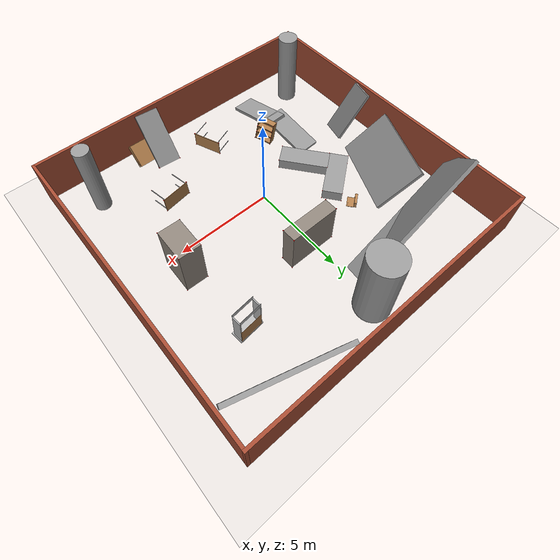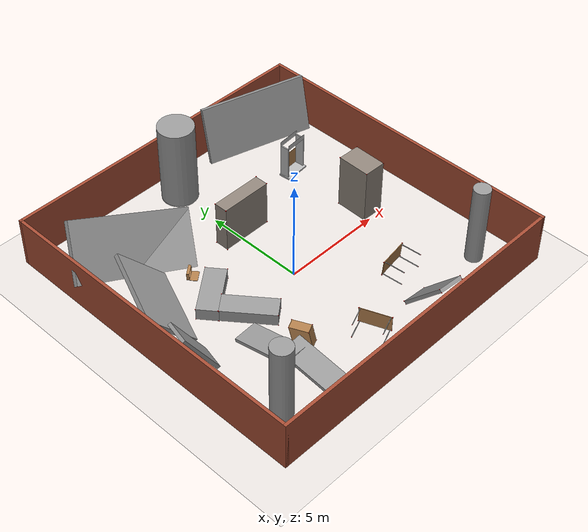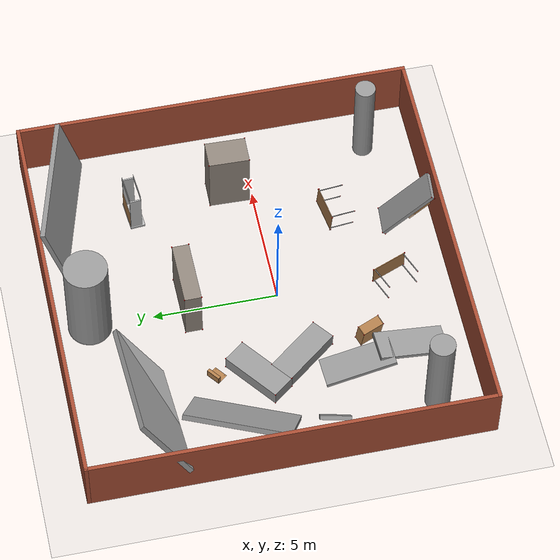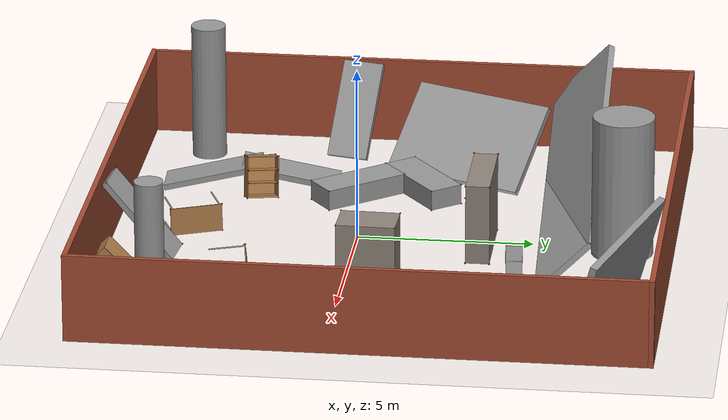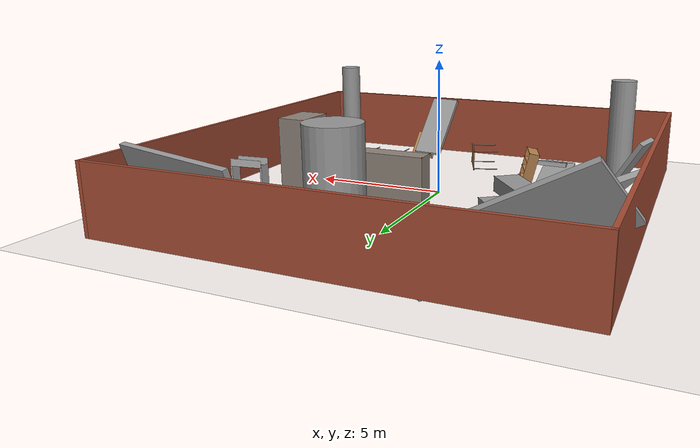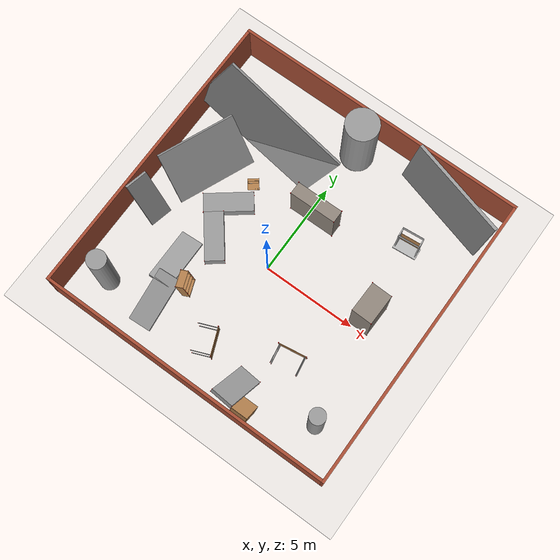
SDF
<sdf version="1.7">
 <world name="tracked_mid360_fastlio_collapse_microdeform_world">
  <gravity>0 0 -9.81</gravity>
  <magnetic_field>6e-06 2.3e-05 -4.2e-05</magnetic_field>
  <atmosphere type="adiabatic"/>
  <physics name="micro_deformation_physics" type="ode">
   <max_step_size>0.01</max_step_size>
   <real_time_update_rate>100</real_time_update_rate>
   <real_time_factor>1</real_time_factor>
   <ode>
    <solver>
     <type>quick</type>
     <iters>80</iters>
     <sor>1.3</sor>
     <use_dynamic_moi_rescaling>0</use_dynamic_moi_rescaling>
    </solver>
    <constraints>
     <cfm>0</cfm>
     <erp>0.2</erp>
     <contact_max_correcting_vel>0.05</contact_max_correcting_vel>
     <contact_surface_layer>0.001</contact_surface_layer>
    </constraints>
   </ode>
  </physics>
  <scene><ambient>0.45 0.45 0.45 1</ambient><background>0.88 0.9 0.94 1</background><shadows>1</shadows></scene>
  <light name="sun" type="directional">
   <pose>0 0 12 0 -0 0</pose>
   <diffuse>0.8 0.8 0.8 1</diffuse>
   <specular>0.2 0.2 0.2 1</specular>
   <attenuation>
    <range>1000</range>
    <constant>0.9</constant>
    <linear>0.01</linear>
    <quadratic>0.001</quadratic>
   </attenuation>
   <direction>-0.45 0.15 -0.88</direction>
   <spot><inner_angle>0</inner_angle><outer_angle>0</outer_angle><falloff>0</falloff></spot>
  </light>
  <spherical_coordinates>
   <surface_model>EARTH_WGS84</surface_model>
   <latitude_deg>0</latitude_deg>
   <longitude_deg>0</longitude_deg>
   <elevation>0</elevation>
   <heading_deg>0</heading_deg>
  </spherical_coordinates>
  <model name="ground_plane">
   <static>1</static>
   <link name="link">
    <collision name="collision">
     <laser_retro>24</laser_retro>
     <geometry><plane><normal>0 0 1</normal><size>100 100</size></plane></geometry>
     <surface>
      <contact>
       <collide_bitmask>65535</collide_bitmask>
       <ode><kp>1e+06</kp><kd>10</kd><max_vel>0.05</max_vel><min_depth>0.001</min_depth></ode>
      </contact>
      <friction><ode><mu>2</mu><mu2>1.5</mu2></ode></friction>
     </surface>
     <max_contacts>20</max_contacts>
    </collision>
    <visual name="visual">
     <cast_shadows>0</cast_shadows>
     <geometry><plane><normal>0 0 1</normal><size>100 100</size></plane></geometry>
     <material>
      <script><uri>file://media/materials/scripts/gazebo.material</uri><name>Gazebo/Grey</name></script>
     </material>
    </visual>
   </link>
  </model>
  <model name="lzg_wall">
   <pose>0.279075 0.9789 0 0 -0 0</pose>
   <link name="Wall_4">
    <collision name="Wall_4_Collision">
     <laser_retro>25</laser_retro>
     <geometry><box><size>16 0.15 2.5</size></box></geometry>
     <pose>0 0 1.25 0 -0 0</pose>
    </collision>
    <visual name="Wall_4_Visual">
     <pose>0 0 1.25 0 -0 0</pose>
     <geometry><box><size>16 0.15 2.5</size></box></geometry>
     <material>
      <script><uri>file://media/materials/scripts/gazebo.material</uri><name>Gazebo/Bricks</name></script>
      <ambient>1 1 1 1</ambient>
     </material>
     <meta><layer>0</layer></meta>
    </visual>
    <pose>0 -7.925 0 0 -0 0</pose>
   </link>
   <link name="Wall_5">
    <collision name="Wall_5_Collision">
     <laser_retro>25</laser_retro>
     <geometry><box><size>16 0.15 2.5</size></box></geometry>
     <pose>0 0 1.25 0 -0 0</pose>
    </collision>
    <visual name="Wall_5_Visual">
     <pose>0 0 1.25 0 -0 0</pose>
     <geometry><box><size>16 0.15 2.5</size></box></geometry>
     <material>
      <script><uri>file://media/materials/scripts/gazebo.material</uri><name>Gazebo/Bricks</name></script>
      <ambient>1 1 1 1</ambient>
     </material>
     <meta><layer>0</layer></meta>
    </visual>
    <pose>7.925 0 0 0 -0 1.5708</pose>
   </link>
   <link name="Wall_6">
    <collision name="Wall_6_Collision">
     <laser_retro>25</laser_retro>
     <geometry><box><size>16 0.15 2.5</size></box></geometry>
     <pose>0 0 1.25 0 -0 0</pose>
    </collision>
    <visual name="Wall_6_Visual">
     <pose>0 0 1.25 0 -0 0</pose>
     <geometry><box><size>16 0.15 2.5</size></box></geometry>
     <material>
      <script><uri>file://media/materials/scripts/gazebo.material</uri><name>Gazebo/Bricks</name></script>
      <ambient>1 1 1 1</ambient>
     </material>
     <meta><layer>0</layer></meta>
    </visual>
    <pose>0 7.925 0 0 -0 3.14159</pose>
   </link>
   <link name="Wall_7">
    <collision name="Wall_7_Collision">
     <laser_retro>25</laser_retro>
     <geometry><box><size>16 0.15 2.5</size></box></geometry>
     <pose>0 0 1.25 0 -0 0</pose>
    </collision>
    <visual name="Wall_7_Visual">
     <pose>0 0 1.25 0 -0 0</pose>
     <geometry><box><size>16 0.15 2.5</size></box></geometry>
     <material>
      <script><uri>file://media/materials/scripts/gazebo.material</uri><name>Gazebo/Bricks</name></script>
      <ambient>1 1 1 1</ambient>
     </material>
     <meta><layer>0</layer></meta>
    </visual>
    <pose>-7.925 0 0 0 -0 -1.5708</pose>
   </link>
   <static>1</static>
  </model>
  <model name="l_shape_target">
   <link name="link">
    <inertial>
     <pose>0 -2e-06 1e-06 0 -0 0</pose>
     <mass>2.9863</mass>
     <inertia>
      <ixx>3.26664</ixx>
      <ixy>-0.962303</ixy>
      <ixz>-0.00190897</ixz>
      <iyy>1.43022</iyy>
      <iyz>-0.00444381</iyz>
      <izz>4.52514</izz>
     </inertia>
    </inertial>
    <visual name="visual_0">
     <pose>-0.373105 -0.868439 -0.001713 0 -0 0</pose>
     <geometry><box><size>2.54222 1 0.58734</size></box></geometry>
     <material>
      <lighting>1</lighting>
      <script><uri>file://media/materials/scripts/gazebo.material</uri><name>Gazebo/Grey</name></script>
      <shader type="pixel"/>
     </material>
    </visual>
    <collision name="collision_0">
     <laser_retro>1</laser_retro>
     <pose>-0.373105 -0.868439 -0.001713 0 -0 0</pose>
     <geometry><box><size>2.54222 1 0.58734</size></box></geometry>
     <surface>
      <friction>
       <ode><mu>1</mu><mu2>1</mu2><fdir1>0 0 0</fdir1><slip1>0</slip1><slip2>0</slip2></ode>
       <torsional>
        <coefficient>1</coefficient>
        <patch_radius>0</patch_radius>
        <surface_radius>0</surface_radius>
        <use_patch_radius>1</use_patch_radius>
        <ode><slip>0</slip></ode>
       </torsional>
      </friction>
      <bounce><restitution_coefficient>0</restitution_coefficient><threshold>1e+06</threshold></bounce>
      <contact>
       <collide_without_contact>0</collide_without_contact>
       <collide_without_contact_bitmask>1</collide_without_contact_bitmask>
       <collide_bitmask>1</collide_bitmask>
       <ode>
        <soft_cfm>0</soft_cfm>
        <soft_erp>0.2</soft_erp>
        <kp>1e+13</kp>
        <kd>1</kd>
        <max_vel>0.01</max_vel>
        <min_depth>0</min_depth>
       </ode>
       <bullet>
        <split_impulse>1</split_impulse>
        <split_impulse_penetration_threshold>-0.01</split_impulse_penetration_threshold>
        <soft_cfm>0</soft_cfm>
        <soft_erp>0.2</soft_erp>
        <kp>1e+13</kp>
        <kd>1</kd>
       </bullet>
      </contact>
     </surface>
    </collision>
    <visual name="visual_1">
     <pose>0.373105 0.868436 0.001714 3.14159 0 -1.56298</pose>
     <geometry><box><size>2.54222 1 0.58734</size></box></geometry>
     <material>
      <lighting>1</lighting>
      <script><uri>file://media/materials/scripts/gazebo.material</uri><name>Gazebo/Grey</name></script>
      <shader type="pixel"/>
     </material>
    </visual>
    <collision name="collision_1">
     <laser_retro>1</laser_retro>
     <pose>0.373105 0.868436 0.001714 3.14159 0 -1.56298</pose>
     <geometry><box><size>2.54222 1 0.58734</size></box></geometry>
     <surface>
      <friction>
       <ode><mu>1</mu><mu2>1</mu2><fdir1>0 0 0</fdir1><slip1>0</slip1><slip2>0</slip2></ode>
       <torsional>
        <coefficient>1</coefficient>
        <patch_radius>0</patch_radius>
        <surface_radius>0</surface_radius>
        <use_patch_radius>1</use_patch_radius>
        <ode><slip>0</slip></ode>
       </torsional>
      </friction>
      <bounce><restitution_coefficient>0</restitution_coefficient><threshold>1e+06</threshold></bounce>
      <contact>
       <collide_without_contact>0</collide_without_contact>
       <collide_without_contact_bitmask>1</collide_without_contact_bitmask>
       <collide_bitmask>1</collide_bitmask>
       <ode>
        <soft_cfm>0</soft_cfm>
        <soft_erp>0.2</soft_erp>
        <kp>1e+13</kp>
        <kd>1</kd>
        <max_vel>0.01</max_vel>
        <min_depth>0</min_depth>
       </ode>
       <bullet>
        <split_impulse>1</split_impulse>
        <split_impulse_penetration_threshold>-0.01</split_impulse_penetration_threshold>
        <soft_cfm>0</soft_cfm>
        <soft_erp>0.2</soft_erp>
        <kp>1e+13</kp>
        <kd>1</kd>
       </bullet>
      </contact>
     </surface>
    </collision>
    <visual name="ground_truth_marker_v_000">
     <pose>-1.64421 -1.36844 -0.295383 0 -0 0</pose>
     <geometry><sphere><radius>0.02</radius></sphere></geometry>
     <material><ambient>1 0 0 1</ambient><diffuse>1 0 0 1</diffuse><emissive>1 0 0 1</emissive></material>
     <cast_shadows>0</cast_shadows>
    </visual>
    <visual name="ground_truth_marker_v_001">
     <pose>-1.64421 -1.36844 0.291957 0 -0 0</pose>
     <geometry><sphere><radius>0.02</radius></sphere></geometry>
     <material><ambient>1 0 0 1</ambient><diffuse>1 0 0 1</diffuse><emissive>1 0 0 1</emissive></material>
     <cast_shadows>0</cast_shadows>
    </visual>
    <visual name="ground_truth_marker_v_002">
     <pose>-1.64421 -0.368439 -0.295383 0 -0 0</pose>
     <geometry><sphere><radius>0.02</radius></sphere></geometry>
     <material><ambient>1 0 0 1</ambient><diffuse>1 0 0 1</diffuse><emissive>1 0 0 1</emissive></material>
     <cast_shadows>0</cast_shadows>
    </visual>
    <visual name="ground_truth_marker_v_003">
     <pose>-1.64421 -0.368439 0.291957 0 -0 0</pose>
     <geometry><sphere><radius>0.02</radius></sphere></geometry>
     <material><ambient>1 0 0 1</ambient><diffuse>1 0 0 1</diffuse><emissive>1 0 0 1</emissive></material>
     <cast_shadows>0</cast_shadows>
    </visual>
    <visual name="ground_truth_marker_v_004">
     <pose>0.898005 -1.36844 -0.295383 0 -0 0</pose>
     <geometry><sphere><radius>0.02</radius></sphere></geometry>
     <material><ambient>1 0 0 1</ambient><diffuse>1 0 0 1</diffuse><emissive>1 0 0 1</emissive></material>
     <cast_shadows>0</cast_shadows>
    </visual>
    <visual name="ground_truth_marker_v_005">
     <pose>0.898005 -1.36844 0.291957 0 -0 0</pose>
     <geometry><sphere><radius>0.02</radius></sphere></geometry>
     <material><ambient>1 0 0 1</ambient><diffuse>1 0 0 1</diffuse><emissive>1 0 0 1</emissive></material>
     <cast_shadows>0</cast_shadows>
    </visual>
    <visual name="ground_truth_marker_v_006">
     <pose>0.898005 -0.368439 -0.295383 0 -0 0</pose>
     <geometry><sphere><radius>0.02</radius></sphere></geometry>
     <material><ambient>1 0 0 1</ambient><diffuse>1 0 0 1</diffuse><emissive>1 0 0 1</emissive></material>
     <cast_shadows>0</cast_shadows>
    </visual>
    <visual name="ground_truth_marker_v_007">
     <pose>0.898005 -0.368439 0.291957 0 -0 0</pose>
     <geometry><sphere><radius>0.02</radius></sphere></geometry>
     <material><ambient>1 0 0 1</ambient><diffuse>1 0 0 1</diffuse><emissive>1 0 0 1</emissive></material>
     <cast_shadows>0</cast_shadows>
    </visual>
    <visual name="ground_truth_marker_v_008">
     <pose>0.863155 2.14342 0.295383 0 -0 0</pose>
     <geometry><sphere><radius>0.02</radius></sphere></geometry>
     <material><ambient>1 0 0 1</ambient><diffuse>1 0 0 1</diffuse><emissive>1 0 0 1</emissive></material>
     <cast_shadows>0</cast_shadows>
    </visual>
    <visual name="ground_truth_marker_v_009">
     <pose>0.863154 2.14342 -0.291957 0 -0 0</pose>
     <geometry><sphere><radius>0.02</radius></sphere></geometry>
     <material><ambient>1 0 0 1</ambient><diffuse>1 0 0 1</diffuse><emissive>1 0 0 1</emissive></material>
     <cast_shadows>0</cast_shadows>
    </visual>
    <visual name="ground_truth_marker_v_010">
     <pose>-0.136814 2.1356 0.295385 0 -0 0</pose>
     <geometry><sphere><radius>0.02</radius></sphere></geometry>
     <material><ambient>1 0 0 1</ambient><diffuse>1 0 0 1</diffuse><emissive>1 0 0 1</emissive></material>
     <cast_shadows>0</cast_shadows>
    </visual>
    <visual name="ground_truth_marker_v_011">
     <pose>-0.136816 2.1356 -0.291955 0 -0 0</pose>
     <geometry><sphere><radius>0.02</radius></sphere></geometry>
     <material><ambient>1 0 0 1</ambient><diffuse>1 0 0 1</diffuse><emissive>1 0 0 1</emissive></material>
     <cast_shadows>0</cast_shadows>
    </visual>
    <visual name="ground_truth_marker_v_012">
     <pose>0.883026 -0.398727 0.295383 0 -0 0</pose>
     <geometry><sphere><radius>0.02</radius></sphere></geometry>
     <material><ambient>1 0 0 1</ambient><diffuse>1 0 0 1</diffuse><emissive>1 0 0 1</emissive></material>
     <cast_shadows>0</cast_shadows>
    </visual>
    <visual name="ground_truth_marker_v_013">
     <pose>0.883024 -0.398727 -0.291957 0 -0 0</pose>
     <geometry><sphere><radius>0.02</radius></sphere></geometry>
     <material><ambient>1 0 0 1</ambient><diffuse>1 0 0 1</diffuse><emissive>1 0 0 1</emissive></material>
     <cast_shadows>0</cast_shadows>
    </visual>
    <visual name="ground_truth_marker_v_014">
     <pose>-0.116944 -0.406543 0.295385 0 -0 0</pose>
     <geometry><sphere><radius>0.02</radius></sphere></geometry>
     <material><ambient>1 0 0 1</ambient><diffuse>1 0 0 1</diffuse><emissive>1 0 0 1</emissive></material>
     <cast_shadows>0</cast_shadows>
    </visual>
    <visual name="ground_truth_marker_v_015">
     <pose>-0.116945 -0.406543 -0.291955 0 -0 0</pose>
     <geometry><sphere><radius>0.02</radius></sphere></geometry>
     <material><ambient>1 0 0 1</ambient><diffuse>1 0 0 1</diffuse><emissive>1 0 0 1</emissive></material>
     <cast_shadows>0</cast_shadows>
    </visual>
    <kinematic>1</kinematic>
   </link>
   <link name="ground_truth_v_000">
    <pose>-1.64421 -1.36844 -0.295383 0 -0 0</pose>
    <inertial>
     <mass>1e-06</mass>
     <inertia><ixx>1e-12</ixx><ixy>0</ixy><ixz>0</ixz><iyy>1e-12</iyy><iyz>0</iyz><izz>1e-12</izz></inertia>
    </inertial>
   </link>
   <link name="ground_truth_v_001">
    <pose>-1.64421 -1.36844 0.291957 0 -0 0</pose>
    <inertial>
     <mass>1e-06</mass>
     <inertia><ixx>1e-12</ixx><ixy>0</ixy><ixz>0</ixz><iyy>1e-12</iyy><iyz>0</iyz><izz>1e-12</izz></inertia>
    </inertial>
   </link>
   <link name="ground_truth_v_002">
    <pose>-1.64421 -0.368439 -0.295383 0 -0 0</pose>
    <inertial>
     <mass>1e-06</mass>
     <inertia><ixx>1e-12</ixx><ixy>0</ixy><ixz>0</ixz><iyy>1e-12</iyy><iyz>0</iyz><izz>1e-12</izz></inertia>
    </inertial>
   </link>
   <link name="ground_truth_v_003">
    <pose>-1.64421 -0.368439 0.291957 0 -0 0</pose>
    <inertial>
     <mass>1e-06</mass>
     <inertia><ixx>1e-12</ixx><ixy>0</ixy><ixz>0</ixz><iyy>1e-12</iyy><iyz>0</iyz><izz>1e-12</izz></inertia>
    </inertial>
   </link>
   <link name="ground_truth_v_004">
    <pose>0.898005 -1.36844 -0.295383 0 -0 0</pose>
    <inertial>
     <mass>1e-06</mass>
     <inertia><ixx>1e-12</ixx><ixy>0</ixy><ixz>0</ixz><iyy>1e-12</iyy><iyz>0</iyz><izz>1e-12</izz></inertia>
    </inertial>
   </link>
   <link name="ground_truth_v_005">
    <pose>0.898005 -1.36844 0.291957 0 -0 0</pose>
    <inertial>
     <mass>1e-06</mass>
     <inertia><ixx>1e-12</ixx><ixy>0</ixy><ixz>0</ixz><iyy>1e-12</iyy><iyz>0</iyz><izz>1e-12</izz></inertia>
    </inertial>
   </link>
   <link name="ground_truth_v_006">
    <pose>0.898005 -0.368439 -0.295383 0 -0 0</pose>
    <inertial>
     <mass>1e-06</mass>
     <inertia><ixx>1e-12</ixx><ixy>0</ixy><ixz>0</ixz><iyy>1e-12</iyy><iyz>0</iyz><izz>1e-12</izz></inertia>
    </inertial>
   </link>
   <link name="ground_truth_v_007">
    <pose>0.898005 -0.368439 0.291957 0 -0 0</pose>
    <inertial>
     <mass>1e-06</mass>
     <inertia><ixx>1e-12</ixx><ixy>0</ixy><ixz>0</ixz><iyy>1e-12</iyy><iyz>0</iyz><izz>1e-12</izz></inertia>
    </inertial>
   </link>
   <link name="ground_truth_v_008">
    <pose>0.863155 2.14342 0.295383 0 -0 0</pose>
    <inertial>
     <mass>1e-06</mass>
     <inertia><ixx>1e-12</ixx><ixy>0</ixy><ixz>0</ixz><iyy>1e-12</iyy><iyz>0</iyz><izz>1e-12</izz></inertia>
    </inertial>
   </link>
   <link name="ground_truth_v_009">
    <pose>0.863154 2.14342 -0.291957 0 -0 0</pose>
    <inertial>
     <mass>1e-06</mass>
     <inertia><ixx>1e-12</ixx><ixy>0</ixy><ixz>0</ixz><iyy>1e-12</iyy><iyz>0</iyz><izz>1e-12</izz></inertia>
    </inertial>
   </link>
   <link name="ground_truth_v_010">
    <pose>-0.136814 2.1356 0.295385 0 -0 0</pose>
    <inertial>
     <mass>1e-06</mass>
     <inertia><ixx>1e-12</ixx><ixy>0</ixy><ixz>0</ixz><iyy>1e-12</iyy><iyz>0</iyz><izz>1e-12</izz></inertia>
    </inertial>
   </link>
   <link name="ground_truth_v_011">
    <pose>-0.136816 2.1356 -0.291955 0 -0 0</pose>
    <inertial>
     <mass>1e-06</mass>
     <inertia><ixx>1e-12</ixx><ixy>0</ixy><ixz>0</ixz><iyy>1e-12</iyy><iyz>0</iyz><izz>1e-12</izz></inertia>
    </inertial>
   </link>
   <link name="ground_truth_v_012">
    <pose>0.883026 -0.398727 0.295383 0 -0 0</pose>
    <inertial>
     <mass>1e-06</mass>
     <inertia><ixx>1e-12</ixx><ixy>0</ixy><ixz>0</ixz><iyy>1e-12</iyy><iyz>0</iyz><izz>1e-12</izz></inertia>
    </inertial>
   </link>
   <link name="ground_truth_v_013">
    <pose>0.883024 -0.398727 -0.291957 0 -0 0</pose>
    <inertial>
     <mass>1e-06</mass>
     <inertia><ixx>1e-12</ixx><ixy>0</ixy><ixz>0</ixz><iyy>1e-12</iyy><iyz>0</iyz><izz>1e-12</izz></inertia>
    </inertial>
   </link>
   <link name="ground_truth_v_014">
    <pose>-0.116944 -0.406543 0.295385 0 -0 0</pose>
    <inertial>
     <mass>1e-06</mass>
     <inertia><ixx>1e-12</ixx><ixy>0</ixy><ixz>0</ixz><iyy>1e-12</iyy><iyz>0</iyz><izz>1e-12</izz></inertia>
    </inertial>
   </link>
   <link name="ground_truth_v_015">
    <pose>-0.116945 -0.406543 -0.291955 0 -0 0</pose>
    <inertial>
     <mass>1e-06</mass>
     <inertia><ixx>1e-12</ixx><ixy>0</ixy><ixz>0</ixz><iyy>1e-12</iyy><iyz>0</iyz><izz>1e-12</izz></inertia>
    </inertial>
   </link>
   <joint name="ground_truth_v_000_fixed_joint" type="fixed">
    <parent>link</parent>
    <child>ground_truth_v_000</child>
   </joint>
   <joint name="ground_truth_v_001_fixed_joint" type="fixed">
    <parent>link</parent>
    <child>ground_truth_v_001</child>
   </joint>
   <joint name="ground_truth_v_002_fixed_joint" type="fixed">
    <parent>link</parent>
    <child>ground_truth_v_002</child>
   </joint>
   <joint name="ground_truth_v_003_fixed_joint" type="fixed">
    <parent>link</parent>
    <child>ground_truth_v_003</child>
   </joint>
   <joint name="ground_truth_v_004_fixed_joint" type="fixed">
    <parent>link</parent>
    <child>ground_truth_v_004</child>
   </joint>
   <joint name="ground_truth_v_005_fixed_joint" type="fixed">
    <parent>link</parent>
    <child>ground_truth_v_005</child>
   </joint>
   <joint name="ground_truth_v_006_fixed_joint" type="fixed">
    <parent>link</parent>
    <child>ground_truth_v_006</child>
   </joint>
   <joint name="ground_truth_v_007_fixed_joint" type="fixed">
    <parent>link</parent>
    <child>ground_truth_v_007</child>
   </joint>
   <joint name="ground_truth_v_008_fixed_joint" type="fixed">
    <parent>link</parent>
    <child>ground_truth_v_008</child>
   </joint>
   <joint name="ground_truth_v_009_fixed_joint" type="fixed">
    <parent>link</parent>
    <child>ground_truth_v_009</child>
   </joint>
   <joint name="ground_truth_v_010_fixed_joint" type="fixed">
    <parent>link</parent>
    <child>ground_truth_v_010</child>
   </joint>
   <joint name="ground_truth_v_011_fixed_joint" type="fixed">
    <parent>link</parent>
    <child>ground_truth_v_011</child>
   </joint>
   <joint name="ground_truth_v_012_fixed_joint" type="fixed">
    <parent>link</parent>
    <child>ground_truth_v_012</child>
   </joint>
   <joint name="ground_truth_v_013_fixed_joint" type="fixed">
    <parent>link</parent>
    <child>ground_truth_v_013</child>
   </joint>
   <joint name="ground_truth_v_014_fixed_joint" type="fixed">
    <parent>link</parent>
    <child>ground_truth_v_014</child>
   </joint>
   <joint name="ground_truth_v_015_fixed_joint" type="fixed">
    <parent>link</parent>
    <child>ground_truth_v_015</child>
   </joint>
   <static>0</static>
   <pose>-3.27675 0.570427 0.295379 0 0 -2.4823</pose>
  </model>
  <model name="frc2016_drawbridge">
   <static>1</static>
   <link name="base">
    <inertial>
     <mass>10</mass>
     <pose>0 0 1 0 -0 0</pose>
     <inertia><ixx>3.64907</ixx><ixy>0</ixy><ixz>0</ixz><iyy>4.67075</iyy><iyz>0</iyz><izz>1.66649</izz></inertia>
    </inertial>
    <visual name="platform">
     <pose>0 0 0.0425 0 -0 0</pose>
     <geometry><box><size>1.27 0.5969 0.085</size></box></geometry>
    </visual>
    <collision name="platform">
     <laser_retro>11</laser_retro>
     <pose>0 0 0.0425 0 -0 0</pose>
     <geometry><box><size>1.27 0.5969 0.085</size></box></geometry>
    </collision>
    <visual name="right_wall">
     <pose>0.55879 0.04444 0.889 0 -0 0</pose>
     <geometry><box><size>0.05715 0.45698 1.77165</size></box></geometry>
    </visual>
    <collision name="right_wall">
     <laser_retro>11</laser_retro>
     <pose>0.55879 0.04444 0.889 0 -0 0</pose>
     <geometry><box><size>0.05715 0.45698 1.77165</size></box></geometry>
    </collision>
    <visual name="left_wall">
     <pose>-0.55879 0.04444 0.889 0 -0 0</pose>
     <geometry><box><size>0.05715 0.45698 1.77165</size></box></geometry>
    </visual>
    <collision name="left_wall">
     <laser_retro>11</laser_retro>
     <pose>-0.55879 0.04444 0.889 0 -0 0</pose>
     <geometry><box><size>0.05715 0.45698 1.77165</size></box></geometry>
    </collision>
    <visual name="front_upper_wall">
     <pose>0 0.27611 1.84286 0 -0 0</pose>
     <geometry><box><size>1.1557 0.006347 0.254</size></box></geometry>
    </visual>
    <collision name="front_upper_wall">
     <laser_retro>11</laser_retro>
     <pose>0 0.27611 1.84286 0 -0 0</pose>
     <geometry><box><size>1.1557 0.006347 0.254</size></box></geometry>
    </collision>
    <visual name="back_upper_wall">
     <pose>0 -0.18722 1.84286 0 -0 0</pose>
     <geometry><box><size>1.1557 0.006347 0.254</size></box></geometry>
    </visual>
    <collision name="back_upper_wall">
     <laser_retro>11</laser_retro>
     <pose>0 -0.18722 1.84286 0 -0 0</pose>
     <geometry><box><size>1.1557 0.006347 0.254</size></box></geometry>
    </collision>
   </link>
   <link name="bridge">
    <pose>0 0.28245 0.50577 0 -0 0</pose>
    <inertial>
     <mass>2</mass>
     <pose>0 -0.28245 -0.50577 0 -0 0</pose>
     <inertia>
      <ixx>0.139361</ixx>
      <ixy>0</ixy>
      <ixz>0</ixz>
      <iyy>0.357088</iyy>
      <iyz>0</iyz>
      <izz>0.217741</izz>
     </inertia>
    </inertial>
    <visual name="visual">
     <geometry><box><size>1.14298 0.006347 0.9144</size></box></geometry>
     <material><script><name>Gazebo/WoodFloor</name><uri>__default__</uri></script></material>
    </visual>
    <collision name="collision">
     <laser_retro>11</laser_retro>
     <geometry><box><size>1.14298 0.006347 0.9144</size></box></geometry>
    </collision>
   </link>
   <joint name="bridge_joint" type="revolute">
    <pose>0 0 -0.4172 0 -0 0</pose>
    <parent>base</parent>
    <child>bridge</child>
    <axis>
     <xyz>1 0 0</xyz>
     <limit><lower>-2</lower><upper>0</upper></limit>
     <dynamics><spring_reference>0</spring_reference><spring_stiffness>0</spring_stiffness></dynamics>
    </axis>
   </joint>
   <pose>4.97332 4.86156 -2.9e-05 0 -0 0.089143</pose>
  </model>
  <model name="lzg_grey_wall">
   <link name="link">
    <pose>7.32515 3.97328 2.49003 0 -0 0</pose>
    <inertial>
     <inertia><ixx>0.477607</ixx><ixy>0</ixy><ixz>0</ixz><iyy>2.2787</iyy><iyz>0</iyz><izz>1.80594</izz></inertia>
     <mass>0.727321</mass>
    </inertial>
    <visual name="visual">
     <cast_shadows>0</cast_shadows>
     <geometry><box><size>5.45491 0.2 2.8</size></box></geometry>
     <material>
      <script>
       <uri>model://grey_wall/materials/scripts</uri>
       <uri>model://grey_wall/materials/textures</uri>
       <name>vrc/grey_wall</name>
      </script>
      <shader type="pixel"/>
     </material>
    </visual>
    <collision name="collision">
     <laser_retro>12</laser_retro>
     <geometry><box><size>5.45491 0.2 2.8</size></box></geometry>
     <surface>
      <friction>
       <ode><mu>1</mu><mu2>1</mu2><fdir1>0 0 0</fdir1><slip1>0</slip1><slip2>0</slip2></ode>
       <torsional>
        <coefficient>1</coefficient>
        <patch_radius>0</patch_radius>
        <surface_radius>0</surface_radius>
        <use_patch_radius>1</use_patch_radius>
        <ode><slip>0</slip></ode>
       </torsional>
      </friction>
      <bounce><restitution_coefficient>0</restitution_coefficient><threshold>1e+06</threshold></bounce>
      <contact>
       <collide_without_contact>0</collide_without_contact>
       <collide_without_contact_bitmask>1</collide_without_contact_bitmask>
       <collide_bitmask>1</collide_bitmask>
       <ode>
        <soft_cfm>0</soft_cfm>
        <soft_erp>0.2</soft_erp>
        <kp>1e+13</kp>
        <kd>1</kd>
        <max_vel>0.01</max_vel>
        <min_depth>0</min_depth>
       </ode>
       <bullet>
        <split_impulse>1</split_impulse>
        <split_impulse_penetration_threshold>-0.01</split_impulse_penetration_threshold>
        <soft_cfm>0</soft_cfm>
        <soft_erp>0.2</soft_erp>
        <kp>1e+13</kp>
        <kd>1</kd>
       </bullet>
      </contact>
     </surface>
    </collision>
   </link>
   <static>1</static>
   <allow_auto_disable>0</allow_auto_disable>
   <pose>-2.92114 5.32308 0.059142 -0.275506 -0 -0.272159</pose>
  </model>
  <model name="wooden_case_metal_peg">
   <static>1</static>
   <frame name="wooden_case::__model__" attached_to="wooden_case::base">
    <pose relative_to="__model__">0 0 0 0 -0 0</pose>
   </frame>
   <link name="wooden_case::base">
    <pose relative_to="wooden_case::__model__">0 0 0.024 0 -0 0</pose>
    <inertial>
     <pose>-0.022184 0 0.171592 0 -0 0</pose>
     <mass>3.96264</mass>
     <inertia>
      <ixx>0.213536</ixx>
      <ixy>0</ixy>
      <ixz>0.000779377</ixz>
      <iyy>0.0708943</iyy>
      <iyz>0</iyz>
      <izz>0.154604</izz>
     </inertia>
    </inertial>
    <collision name="collision_back">
     <laser_retro>13</laser_retro>
     <pose>-0.053975 0 0.1778 0 -0 0</pose>
     <geometry><box><size>0.01905 0.5461 0.3175</size></box></geometry>
     <surface>
      <contact>
       <poissons_ratio>0.347</poissons_ratio>
       <elastic_modulus>8.8e+09</elastic_modulus>
       <ode><kp>100000</kp><kd>100</kd><max_vel>100</max_vel><min_depth>0.001</min_depth></ode>
      </contact>
      <friction>
       <torsional>
        <coefficient>1</coefficient>
        <use_patch_radius>0</use_patch_radius>
        <surface_radius>0.01</surface_radius>
       </torsional>
      </friction>
     </surface>
    </collision>
    <visual name="visual_back">
     <pose>-0.053975 0 0.1778 0 -0 0</pose>
     <geometry><box><size>0.01905 0.5461 0.3175</size></box></geometry>
     <material>
      <script><uri>file://media/materials/scripts/gazebo.material</uri><name>Gazebo/Wood</name></script>
     </material>
    </visual>
    <collision name="collision_bottom">
     <laser_retro>13</laser_retro>
     <pose>0 0 0.009525 0 -0 0</pose>
     <geometry><box><size>0.127 0.5842 0.01905</size></box></geometry>
     <surface>
      <contact>
       <poissons_ratio>0.347</poissons_ratio>
       <elastic_modulus>8.8e+09</elastic_modulus>
       <ode><kp>100000</kp><kd>100</kd><max_vel>100</max_vel><min_depth>0.001</min_depth></ode>
      </contact>
      <friction>
       <torsional>
        <coefficient>1</coefficient>
        <use_patch_radius>0</use_patch_radius>
        <surface_radius>0.01</surface_radius>
       </torsional>
      </friction>
     </surface>
    </collision>
    <visual name="visual_bottom">
     <pose>0 0 0.009525 0 -0 0</pose>
     <geometry><box><size>0.127 0.5842 0.01905</size></box></geometry>
     <material>
      <script><uri>file://media/materials/scripts/gazebo.material</uri><name>Gazebo/Wood</name></script>
     </material>
    </visual>
    <collision name="collision_top">
     <laser_retro>13</laser_retro>
     <pose>0 0 0.346075 0 -0 0</pose>
     <geometry><box><size>0.127 0.5842 0.01905</size></box></geometry>
     <surface>
      <contact>
       <poissons_ratio>0.347</poissons_ratio>
       <elastic_modulus>8.8e+09</elastic_modulus>
       <ode><kp>100000</kp><kd>100</kd><max_vel>100</max_vel><min_depth>0.001</min_depth></ode>
      </contact>
      <friction>
       <torsional>
        <coefficient>1</coefficient>
        <use_patch_radius>0</use_patch_radius>
        <surface_radius>0.01</surface_radius>
       </torsional>
      </friction>
     </surface>
    </collision>
    <visual name="visual_top">
     <pose>0 0 0.346075 0 -0 0</pose>
     <geometry><box><size>0.127 0.5842 0.01905</size></box></geometry>
     <material>
      <script><uri>file://media/materials/scripts/gazebo.material</uri><name>Gazebo/Wood</name></script>
     </material>
    </visual>
    <collision name="collision_left">
     <laser_retro>13</laser_retro>
     <pose>0 -0.282575 0.1778 0 -0 0</pose>
     <geometry><box><size>0.127 0.01905 0.3175</size></box></geometry>
     <surface>
      <contact>
       <poissons_ratio>0.347</poissons_ratio>
       <elastic_modulus>8.8e+09</elastic_modulus>
       <ode><kp>100000</kp><kd>100</kd><max_vel>100</max_vel><min_depth>0.001</min_depth></ode>
      </contact>
      <friction>
       <torsional>
        <coefficient>1</coefficient>
        <use_patch_radius>0</use_patch_radius>
        <surface_radius>0.01</surface_radius>
       </torsional>
      </friction>
     </surface>
    </collision>
    <visual name="visual_left">
     <pose>0 -0.282575 0.1778 0 -0 0</pose>
     <geometry><box><size>0.127 0.01905 0.3175</size></box></geometry>
     <material>
      <script><uri>file://media/materials/scripts/gazebo.material</uri><name>Gazebo/Wood</name></script>
     </material>
    </visual>
    <collision name="collision_right">
     <laser_retro>13</laser_retro>
     <pose>0 0.282575 0.1778 0 -0 0</pose>
     <geometry><box><size>0.127 0.01905 0.3175</size></box></geometry>
     <surface>
      <contact>
       <poissons_ratio>0.347</poissons_ratio>
       <elastic_modulus>8.8e+09</elastic_modulus>
       <ode><kp>100000</kp><kd>100</kd><max_vel>100</max_vel><min_depth>0.001</min_depth></ode>
      </contact>
      <friction>
       <torsional>
        <coefficient>1</coefficient>
        <use_patch_radius>0</use_patch_radius>
        <surface_radius>0.01</surface_radius>
       </torsional>
      </friction>
     </surface>
    </collision>
    <visual name="visual_right">
     <pose>0 0.282575 0.1778 0 -0 0</pose>
     <geometry><box><size>0.127 0.01905 0.3175</size></box></geometry>
     <material>
      <script><uri>file://media/materials/scripts/gazebo.material</uri><name>Gazebo/Wood</name></script>
     </material>
    </visual>
    <collision name="collision_block_left">
     <laser_retro>13</laser_retro>
     <pose>0.0095 -0.2151 -0.012 0 -0 0</pose>
     <geometry><box><size>0.108 0.05 0.024</size></box></geometry>
     <surface>
      <contact>
       <poissons_ratio>0.347</poissons_ratio>
       <elastic_modulus>8.8e+09</elastic_modulus>
       <ode><kp>100000</kp><kd>100</kd><max_vel>100</max_vel><min_depth>0.001</min_depth></ode>
      </contact>
      <friction>
       <torsional>
        <coefficient>1</coefficient>
        <use_patch_radius>0</use_patch_radius>
        <surface_radius>0.01</surface_radius>
       </torsional>
      </friction>
     </surface>
    </collision>
    <visual name="visual_block_left">
     <pose>0.0095 -0.2151 -0.012 0 -0 0</pose>
     <geometry><box><size>0.108 0.05 0.024</size></box></geometry>
     <material>
      <script><uri>file://media/materials/scripts/gazebo.material</uri><name>Gazebo/Wood</name></script>
     </material>
    </visual>
    <collision name="collision_block_right">
     <laser_retro>13</laser_retro>
     <pose>0.0095 0.2151 -0.012 0 -0 0</pose>
     <geometry><box><size>0.108 0.05 0.024</size></box></geometry>
     <surface>
      <contact>
       <poissons_ratio>0.347</poissons_ratio>
       <elastic_modulus>8.8e+09</elastic_modulus>
       <ode><kp>100000</kp><kd>100</kd><max_vel>100</max_vel><min_depth>0.001</min_depth></ode>
      </contact>
      <friction>
       <torsional>
        <coefficient>1</coefficient>
        <use_patch_radius>0</use_patch_radius>
        <surface_radius>0.01</surface_radius>
       </torsional>
      </friction>
     </surface>
    </collision>
    <visual name="visual_block_right">
     <pose>0.0095 0.2151 -0.012 0 -0 0</pose>
     <geometry><box><size>0.108 0.05 0.024</size></box></geometry>
     <material>
      <script><uri>file://media/materials/scripts/gazebo.material</uri><name>Gazebo/Wood</name></script>
     </material>
    </visual>
   </link>
   <link name="wooden_case::lid">
    <pose relative_to="wooden_case::__model__">0.243775 0 0.009525 0 -0 0</pose>
    <inertial>
     <mass>1.97874</mass>
     <inertia>
      <ixx>0.0563367</ixx>
      <ixy>0</ixy>
      <ixz>0</ixz>
      <iyy>0.020911</iyy>
      <iyz>0</iyz>
      <izz>0.0771281</izz>
     </inertia>
    </inertial>
    <collision name="collision">
     <laser_retro>13</laser_retro>
     <geometry><box><size>0.3556 0.5842 0.01905</size></box></geometry>
     <surface>
      <contact>
       <poissons_ratio>0.347</poissons_ratio>
       <elastic_modulus>8.8e+09</elastic_modulus>
       <ode><kp>100000</kp><kd>100</kd><max_vel>100</max_vel><min_depth>0.001</min_depth></ode>
      </contact>
      <friction>
       <torsional>
        <coefficient>1</coefficient>
        <use_patch_radius>0</use_patch_radius>
        <surface_radius>0.01</surface_radius>
       </torsional>
      </friction>
     </surface>
    </collision>
    <visual name="visual">
     <geometry><box><size>0.3556 0.5842 0.01905</size></box></geometry>
     <material>
      <script><uri>file://media/materials/scripts/gazebo.material</uri><name>Gazebo/Wood</name></script>
     </material>
    </visual>
    <visual name="tee_nut_1">
     <pose>0.122 -0.216 0 0 -0 0</pose>
     <geometry><cylinder><radius>0.00635</radius><length>0.0192405</length></cylinder></geometry>
     <material>
      <script><uri>file://media/materials/scripts/gazebo.material</uri><name>Gazebo/Grey</name></script>
     </material>
    </visual>
    <visual name="tee_nut_2">
     <pose>0.122 -0.088 0 0 -0 0</pose>
     <geometry><cylinder><radius>0.00635</radius><length>0.0192405</length></cylinder></geometry>
     <material>
      <script><uri>file://media/materials/scripts/gazebo.material</uri><name>Gazebo/Grey</name></script>
     </material>
    </visual>
    <visual name="tee_nut_3">
     <pose>0.122 0.088 0 0 -0 0</pose>
     <geometry><cylinder><radius>0.00635</radius><length>0.0192405</length></cylinder></geometry>
     <material>
      <script><uri>file://media/materials/scripts/gazebo.material</uri><name>Gazebo/Grey</name></script>
     </material>
    </visual>
    <visual name="tee_nut_4">
     <pose>0.122 0.216 0 0 -0 0</pose>
     <geometry><cylinder><radius>0.00635</radius><length>0.0192405</length></cylinder></geometry>
     <material>
      <script><uri>file://media/materials/scripts/gazebo.material</uri><name>Gazebo/Grey</name></script>
     </material>
    </visual>
   </link>
   <joint name="wooden_case::lid_hinge" type="revolute">
    <pose>-0.1778 0 0.01905 0 -0 0</pose>
    <parent>wooden_case::base</parent>
    <child>wooden_case::lid</child>
    <axis>
     <xyz>0 1 0</xyz>
     <limit><upper>0.523599</upper><lower>-1.5708</lower></limit>
     <dynamics><spring_reference>0</spring_reference><spring_stiffness>0</spring_stiffness></dynamics>
    </axis>
   </joint>
   <frame name="peg::__model__" attached_to="peg::link">
    <pose relative_to="__model__">0.365774 0.216 0.01905 0 -0 0</pose>
   </frame>
   <link name="peg::link">
    <pose relative_to="peg::__model__">0 0 0.031 0 -0 0</pose>
    <inertial>
     <mass>0.0121</mass>
     <inertia>
      <ixx>3.90898e-06</ixx>
      <ixy>0</ixy>
      <ixz>0</ixz>
      <iyy>3.90898e-06</iyy>
      <iyz>0</iyz>
      <izz>6.58845e-08</izz>
     </inertia>
    </inertial>
    <collision name="collision">
     <laser_retro>13</laser_retro>
     <geometry><cylinder><radius>0.0033</radius><length>0.062</length></cylinder></geometry>
     <surface>
      <contact>
       <poissons_ratio>0.305</poissons_ratio>
       <elastic_modulus>2e+11</elastic_modulus>
       <ode><kp>100000</kp><kd>100</kd><max_vel>100</max_vel><min_depth>0.001</min_depth></ode>
      </contact>
      <friction>
       <torsional>
        <coefficient>1</coefficient>
        <use_patch_radius>0</use_patch_radius>
        <surface_radius>0.01</surface_radius>
       </torsional>
      </friction>
     </surface>
    </collision>
    <visual name="visual">
     <geometry><cylinder><radius>0.0033</radius><length>0.062</length></cylinder></geometry>
     <material>
      <script><uri>file://media/materials/scripts/gazebo.material</uri><name>Gazebo/Grey</name></script>
     </material>
    </visual>
   </link>
   <joint name="case_peg" type="revolute">
    <child>peg::link</child>
    <parent>wooden_case::lid</parent>
    <axis>
     <xyz>0 0 1</xyz>
     <limit><upper>0</upper><lower>0</lower></limit>
     <dynamics><spring_reference>0</spring_reference><spring_stiffness>0</spring_stiffness></dynamics>
    </axis>
   </joint>
   <pose>-3.2677 3.21042 -0.001063 1.1e-05 -0.000531 -0.909382</pose>
  </model>
  <model name="bookshelf">
   <static>0</static>
   <link name="link">
    <inertial>
     <mass>1</mass>
     <inertia><ixx>1</ixx><ixy>0</ixy><ixz>0</ixz><iyy>1</iyy><iyz>0</iyz><izz>1</izz></inertia>
    </inertial>
    <collision name="back">
     <laser_retro>10</laser_retro>
     <pose>0 0.005 0.6 0 -0 0</pose>
     <geometry><box><size>0.9 0.01 1.2</size></box></geometry>
    </collision>
    <visual name="visual1">
     <pose>0 0.005 0.6 0 -0 0</pose>
     <geometry><box><size>0.9 0.01 1.2</size></box></geometry>
     <material>
      <script><uri>file://media/materials/scripts/gazebo.material</uri><name>Gazebo/Wood</name></script>
     </material>
    </visual>
    <collision name="left_side">
     <laser_retro>10</laser_retro>
     <pose>0.45 -0.195 0.6 0 -0 0</pose>
     <geometry><box><size>0.02 0.4 1.2</size></box></geometry>
    </collision>
    <visual name="visual2">
     <pose>0.45 -0.195 0.6 0 -0 0</pose>
     <geometry><box><size>0.02 0.4 1.2</size></box></geometry>
     <material>
      <script><uri>file://media/materials/scripts/gazebo.material</uri><name>Gazebo/Wood</name></script>
     </material>
    </visual>
    <collision name="right_side">
     <laser_retro>10</laser_retro>
     <pose>-0.45 -0.195 0.6 0 -0 0</pose>
     <geometry><box><size>0.02 0.4 1.2</size></box></geometry>
    </collision>
    <visual name="visual3">
     <pose>-0.45 -0.195 0.6 0 -0 0</pose>
     <geometry><box><size>0.02 0.4 1.2</size></box></geometry>
     <material>
      <script><uri>file://media/materials/scripts/gazebo.material</uri><name>Gazebo/Wood</name></script>
     </material>
    </visual>
    <collision name="bottom">
     <laser_retro>10</laser_retro>
     <pose>0 -0.195 0.03 0 -0 0</pose>
     <geometry><box><size>0.88 0.4 0.06</size></box></geometry>
    </collision>
    <visual name="visual4">
     <pose>0 -0.195 0.03 0 -0 0</pose>
     <geometry><box><size>0.88 0.4 0.06</size></box></geometry>
     <material>
      <script><uri>file://media/materials/scripts/gazebo.material</uri><name>Gazebo/Wood</name></script>
     </material>
    </visual>
    <collision name="top">
     <laser_retro>10</laser_retro>
     <pose>0 -0.195 1.19 0 -0 0</pose>
     <geometry><box><size>0.88 0.4 0.02</size></box></geometry>
    </collision>
    <visual name="visual5">
     <pose>0 -0.195 1.19 0 -0 0</pose>
     <geometry><box><size>0.88 0.4 0.02</size></box></geometry>
     <material>
      <script><uri>file://media/materials/scripts/gazebo.material</uri><name>Gazebo/Wood</name></script>
     </material>
    </visual>
    <collision name="low_shelf">
     <laser_retro>10</laser_retro>
     <pose>0 -0.195 0.43 0 -0 0</pose>
     <geometry><box><size>0.88 0.4 0.02</size></box></geometry>
    </collision>
    <visual name="visual6">
     <pose>0 -0.195 0.43 0 -0 0</pose>
     <geometry><box><size>0.88 0.4 0.02</size></box></geometry>
     <material>
      <script><uri>file://media/materials/scripts/gazebo.material</uri><name>Gazebo/Wood</name></script>
     </material>
    </visual>
    <collision name="high_shelf">
     <laser_retro>10</laser_retro>
     <pose>0 -0.195 0.8 0 -0 0</pose>
     <geometry><box><size>0.88 0.4 0.02</size></box></geometry>
    </collision>
    <visual name="visual7">
     <pose>0 -0.195 0.8 0 -0 0</pose>
     <geometry><box><size>0.88 0.4 0.02</size></box></geometry>
     <material>
      <script><uri>file://media/materials/scripts/gazebo.material</uri><name>Gazebo/Wood</name></script>
     </material>
    </visual>
    <visual name="ground_truth_marker_v_000">
     <pose>-0.46 -0.395 0 0 -0 0</pose>
     <geometry><sphere><radius>0.02</radius></sphere></geometry>
     <material><ambient>1 0 0 1</ambient><diffuse>1 0 0 1</diffuse><emissive>1 0 0 1</emissive></material>
     <cast_shadows>0</cast_shadows>
    </visual>
    <visual name="ground_truth_marker_v_001">
     <pose>-0.46 -0.395 1.2 0 -0 0</pose>
     <geometry><sphere><radius>0.02</radius></sphere></geometry>
     <material><ambient>1 0 0 1</ambient><diffuse>1 0 0 1</diffuse><emissive>1 0 0 1</emissive></material>
     <cast_shadows>0</cast_shadows>
    </visual>
    <visual name="ground_truth_marker_v_002">
     <pose>0.46 -0.395 0 0 -0 0</pose>
     <geometry><sphere><radius>0.02</radius></sphere></geometry>
     <material><ambient>1 0 0 1</ambient><diffuse>1 0 0 1</diffuse><emissive>1 0 0 1</emissive></material>
     <cast_shadows>0</cast_shadows>
    </visual>
    <visual name="ground_truth_marker_v_003">
     <pose>0.46 -0.395 1.2 0 -0 0</pose>
     <geometry><sphere><radius>0.02</radius></sphere></geometry>
     <material><ambient>1 0 0 1</ambient><diffuse>1 0 0 1</diffuse><emissive>1 0 0 1</emissive></material>
     <cast_shadows>0</cast_shadows>
    </visual>
    <visual name="ground_truth_marker_v_004">
     <pose>-0.45 0.01 0 0 -0 0</pose>
     <geometry><sphere><radius>0.02</radius></sphere></geometry>
     <material><ambient>1 0 0 1</ambient><diffuse>1 0 0 1</diffuse><emissive>1 0 0 1</emissive></material>
     <cast_shadows>0</cast_shadows>
    </visual>
    <visual name="ground_truth_marker_v_005">
     <pose>-0.45 0.01 1.2 0 -0 0</pose>
     <geometry><sphere><radius>0.02</radius></sphere></geometry>
     <material><ambient>1 0 0 1</ambient><diffuse>1 0 0 1</diffuse><emissive>1 0 0 1</emissive></material>
     <cast_shadows>0</cast_shadows>
    </visual>
    <visual name="ground_truth_marker_v_006">
     <pose>0.45 0.01 0 0 -0 0</pose>
     <geometry><sphere><radius>0.02</radius></sphere></geometry>
     <material><ambient>1 0 0 1</ambient><diffuse>1 0 0 1</diffuse><emissive>1 0 0 1</emissive></material>
     <cast_shadows>0</cast_shadows>
    </visual>
    <visual name="ground_truth_marker_v_007">
     <pose>0.45 0.01 1.2 0 -0 0</pose>
     <geometry><sphere><radius>0.02</radius></sphere></geometry>
     <material><ambient>1 0 0 1</ambient><diffuse>1 0 0 1</diffuse><emissive>1 0 0 1</emissive></material>
     <cast_shadows>0</cast_shadows>
    </visual>
    <visual name="ground_truth_marker_v_008">
     <pose>-0.44 -0.395 0.42 0 -0 0</pose>
     <geometry><sphere><radius>0.02</radius></sphere></geometry>
     <material><ambient>1 0 0 1</ambient><diffuse>1 0 0 1</diffuse><emissive>1 0 0 1</emissive></material>
     <cast_shadows>0</cast_shadows>
    </visual>
    <visual name="ground_truth_marker_v_009">
     <pose>-0.44 -0.395 0.44 0 -0 0</pose>
     <geometry><sphere><radius>0.02</radius></sphere></geometry>
     <material><ambient>1 0 0 1</ambient><diffuse>1 0 0 1</diffuse><emissive>1 0 0 1</emissive></material>
     <cast_shadows>0</cast_shadows>
    </visual>
    <visual name="ground_truth_marker_v_010">
     <pose>0.44 -0.395 0.42 0 -0 0</pose>
     <geometry><sphere><radius>0.02</radius></sphere></geometry>
     <material><ambient>1 0 0 1</ambient><diffuse>1 0 0 1</diffuse><emissive>1 0 0 1</emissive></material>
     <cast_shadows>0</cast_shadows>
    </visual>
    <visual name="ground_truth_marker_v_011">
     <pose>0.44 -0.395 0.44 0 -0 0</pose>
     <geometry><sphere><radius>0.02</radius></sphere></geometry>
     <material><ambient>1 0 0 1</ambient><diffuse>1 0 0 1</diffuse><emissive>1 0 0 1</emissive></material>
     <cast_shadows>0</cast_shadows>
    </visual>
    <visual name="ground_truth_marker_v_012">
     <pose>-0.44 -0.395 0.79 0 -0 0</pose>
     <geometry><sphere><radius>0.02</radius></sphere></geometry>
     <material><ambient>1 0 0 1</ambient><diffuse>1 0 0 1</diffuse><emissive>1 0 0 1</emissive></material>
     <cast_shadows>0</cast_shadows>
    </visual>
    <visual name="ground_truth_marker_v_013">
     <pose>-0.44 -0.395 0.81 0 -0 0</pose>
     <geometry><sphere><radius>0.02</radius></sphere></geometry>
     <material><ambient>1 0 0 1</ambient><diffuse>1 0 0 1</diffuse><emissive>1 0 0 1</emissive></material>
     <cast_shadows>0</cast_shadows>
    </visual>
    <visual name="ground_truth_marker_v_014">
     <pose>0.44 -0.395 0.79 0 -0 0</pose>
     <geometry><sphere><radius>0.02</radius></sphere></geometry>
     <material><ambient>1 0 0 1</ambient><diffuse>1 0 0 1</diffuse><emissive>1 0 0 1</emissive></material>
     <cast_shadows>0</cast_shadows>
    </visual>
    <visual name="ground_truth_marker_v_015">
     <pose>0.44 -0.395 0.81 0 -0 0</pose>
     <geometry><sphere><radius>0.02</radius></sphere></geometry>
     <material><ambient>1 0 0 1</ambient><diffuse>1 0 0 1</diffuse><emissive>1 0 0 1</emissive></material>
     <cast_shadows>0</cast_shadows>
    </visual>
    <kinematic>1</kinematic>
   </link>
   <link name="ground_truth_v_000">
    <pose>-0.46 -0.395 0 0 -0 0</pose>
    <inertial>
     <mass>1e-06</mass>
     <inertia><ixx>1e-12</ixx><ixy>0</ixy><ixz>0</ixz><iyy>1e-12</iyy><iyz>0</iyz><izz>1e-12</izz></inertia>
    </inertial>
   </link>
   <link name="ground_truth_v_001">
    <pose>-0.46 -0.395 1.2 0 -0 0</pose>
    <inertial>
     <mass>1e-06</mass>
     <inertia><ixx>1e-12</ixx><ixy>0</ixy><ixz>0</ixz><iyy>1e-12</iyy><iyz>0</iyz><izz>1e-12</izz></inertia>
    </inertial>
   </link>
   <link name="ground_truth_v_002">
    <pose>0.46 -0.395 0 0 -0 0</pose>
    <inertial>
     <mass>1e-06</mass>
     <inertia><ixx>1e-12</ixx><ixy>0</ixy><ixz>0</ixz><iyy>1e-12</iyy><iyz>0</iyz><izz>1e-12</izz></inertia>
    </inertial>
   </link>
   <link name="ground_truth_v_003">
    <pose>0.46 -0.395 1.2 0 -0 0</pose>
    <inertial>
     <mass>1e-06</mass>
     <inertia><ixx>1e-12</ixx><ixy>0</ixy><ixz>0</ixz><iyy>1e-12</iyy><iyz>0</iyz><izz>1e-12</izz></inertia>
    </inertial>
   </link>
   <link name="ground_truth_v_004">
    <pose>-0.45 0.01 0 0 -0 0</pose>
    <inertial>
     <mass>1e-06</mass>
     <inertia><ixx>1e-12</ixx><ixy>0</ixy><ixz>0</ixz><iyy>1e-12</iyy><iyz>0</iyz><izz>1e-12</izz></inertia>
    </inertial>
   </link>
   <link name="ground_truth_v_005">
    <pose>-0.45 0.01 1.2 0 -0 0</pose>
    <inertial>
     <mass>1e-06</mass>
     <inertia><ixx>1e-12</ixx><ixy>0</ixy><ixz>0</ixz><iyy>1e-12</iyy><iyz>0</iyz><izz>1e-12</izz></inertia>
    </inertial>
   </link>
   <link name="ground_truth_v_006">
    <pose>0.45 0.01 0 0 -0 0</pose>
    <inertial>
     <mass>1e-06</mass>
     <inertia><ixx>1e-12</ixx><ixy>0</ixy><ixz>0</ixz><iyy>1e-12</iyy><iyz>0</iyz><izz>1e-12</izz></inertia>
    </inertial>
   </link>
   <link name="ground_truth_v_007">
    <pose>0.45 0.01 1.2 0 -0 0</pose>
    <inertial>
     <mass>1e-06</mass>
     <inertia><ixx>1e-12</ixx><ixy>0</ixy><ixz>0</ixz><iyy>1e-12</iyy><iyz>0</iyz><izz>1e-12</izz></inertia>
    </inertial>
   </link>
   <link name="ground_truth_v_008">
    <pose>-0.44 -0.395 0.42 0 -0 0</pose>
    <inertial>
     <mass>1e-06</mass>
     <inertia><ixx>1e-12</ixx><ixy>0</ixy><ixz>0</ixz><iyy>1e-12</iyy><iyz>0</iyz><izz>1e-12</izz></inertia>
    </inertial>
   </link>
   <link name="ground_truth_v_009">
    <pose>-0.44 -0.395 0.44 0 -0 0</pose>
    <inertial>
     <mass>1e-06</mass>
     <inertia><ixx>1e-12</ixx><ixy>0</ixy><ixz>0</ixz><iyy>1e-12</iyy><iyz>0</iyz><izz>1e-12</izz></inertia>
    </inertial>
   </link>
   <link name="ground_truth_v_010">
    <pose>0.44 -0.395 0.42 0 -0 0</pose>
    <inertial>
     <mass>1e-06</mass>
     <inertia><ixx>1e-12</ixx><ixy>0</ixy><ixz>0</ixz><iyy>1e-12</iyy><iyz>0</iyz><izz>1e-12</izz></inertia>
    </inertial>
   </link>
   <link name="ground_truth_v_011">
    <pose>0.44 -0.395 0.44 0 -0 0</pose>
    <inertial>
     <mass>1e-06</mass>
     <inertia><ixx>1e-12</ixx><ixy>0</ixy><ixz>0</ixz><iyy>1e-12</iyy><iyz>0</iyz><izz>1e-12</izz></inertia>
    </inertial>
   </link>
   <link name="ground_truth_v_012">
    <pose>-0.44 -0.395 0.79 0 -0 0</pose>
    <inertial>
     <mass>1e-06</mass>
     <inertia><ixx>1e-12</ixx><ixy>0</ixy><ixz>0</ixz><iyy>1e-12</iyy><iyz>0</iyz><izz>1e-12</izz></inertia>
    </inertial>
   </link>
   <link name="ground_truth_v_013">
    <pose>-0.44 -0.395 0.81 0 -0 0</pose>
    <inertial>
     <mass>1e-06</mass>
     <inertia><ixx>1e-12</ixx><ixy>0</ixy><ixz>0</ixz><iyy>1e-12</iyy><iyz>0</iyz><izz>1e-12</izz></inertia>
    </inertial>
   </link>
   <link name="ground_truth_v_014">
    <pose>0.44 -0.395 0.79 0 -0 0</pose>
    <inertial>
     <mass>1e-06</mass>
     <inertia><ixx>1e-12</ixx><ixy>0</ixy><ixz>0</ixz><iyy>1e-12</iyy><iyz>0</iyz><izz>1e-12</izz></inertia>
    </inertial>
   </link>
   <link name="ground_truth_v_015">
    <pose>0.44 -0.395 0.81 0 -0 0</pose>
    <inertial>
     <mass>1e-06</mass>
     <inertia><ixx>1e-12</ixx><ixy>0</ixy><ixz>0</ixz><iyy>1e-12</iyy><iyz>0</iyz><izz>1e-12</izz></inertia>
    </inertial>
   </link>
   <joint name="ground_truth_v_000_fixed_joint" type="fixed">
    <parent>link</parent>
    <child>ground_truth_v_000</child>
   </joint>
   <joint name="ground_truth_v_001_fixed_joint" type="fixed">
    <parent>link</parent>
    <child>ground_truth_v_001</child>
   </joint>
   <joint name="ground_truth_v_002_fixed_joint" type="fixed">
    <parent>link</parent>
    <child>ground_truth_v_002</child>
   </joint>
   <joint name="ground_truth_v_003_fixed_joint" type="fixed">
    <parent>link</parent>
    <child>ground_truth_v_003</child>
   </joint>
   <joint name="ground_truth_v_004_fixed_joint" type="fixed">
    <parent>link</parent>
    <child>ground_truth_v_004</child>
   </joint>
   <joint name="ground_truth_v_005_fixed_joint" type="fixed">
    <parent>link</parent>
    <child>ground_truth_v_005</child>
   </joint>
   <joint name="ground_truth_v_006_fixed_joint" type="fixed">
    <parent>link</parent>
    <child>ground_truth_v_006</child>
   </joint>
   <joint name="ground_truth_v_007_fixed_joint" type="fixed">
    <parent>link</parent>
    <child>ground_truth_v_007</child>
   </joint>
   <joint name="ground_truth_v_008_fixed_joint" type="fixed">
    <parent>link</parent>
    <child>ground_truth_v_008</child>
   </joint>
   <joint name="ground_truth_v_009_fixed_joint" type="fixed">
    <parent>link</parent>
    <child>ground_truth_v_009</child>
   </joint>
   <joint name="ground_truth_v_010_fixed_joint" type="fixed">
    <parent>link</parent>
    <child>ground_truth_v_010</child>
   </joint>
   <joint name="ground_truth_v_011_fixed_joint" type="fixed">
    <parent>link</parent>
    <child>ground_truth_v_011</child>
   </joint>
   <joint name="ground_truth_v_012_fixed_joint" type="fixed">
    <parent>link</parent>
    <child>ground_truth_v_012</child>
   </joint>
   <joint name="ground_truth_v_013_fixed_joint" type="fixed">
    <parent>link</parent>
    <child>ground_truth_v_013</child>
   </joint>
   <joint name="ground_truth_v_014_fixed_joint" type="fixed">
    <parent>link</parent>
    <child>ground_truth_v_014</child>
   </joint>
   <joint name="ground_truth_v_015_fixed_joint" type="fixed">
    <parent>link</parent>
    <child>ground_truth_v_015</child>
   </joint>
   <pose>-2.73269 -3.15697 0 -0.229313 0.074467 1.93675</pose>
  </model>
  <model name="bookshelf_0">
   <static>1</static>
   <link name="link">
    <inertial><mass>1</mass></inertial>
    <collision name="back">
     <laser_retro>15</laser_retro>
     <pose>0 0.005 0.6 0 -0 0</pose>
     <geometry><box><size>0.9 0.01 1.2</size></box></geometry>
    </collision>
    <visual name="visual1">
     <pose>0 0.005 0.6 0 -0 0</pose>
     <geometry><box><size>0.9 0.01 1.2</size></box></geometry>
     <material>
      <script><uri>file://media/materials/scripts/gazebo.material</uri><name>Gazebo/Wood</name></script>
     </material>
    </visual>
    <collision name="left_side">
     <laser_retro>15</laser_retro>
     <pose>0.45 -0.195 0.6 0 -0 0</pose>
     <geometry><box><size>0.02 0.4 1.2</size></box></geometry>
    </collision>
    <visual name="visual2">
     <pose>0.45 -0.195 0.6 0 -0 0</pose>
     <geometry><box><size>0.02 0.4 1.2</size></box></geometry>
     <material>
      <script><uri>file://media/materials/scripts/gazebo.material</uri><name>Gazebo/Wood</name></script>
     </material>
    </visual>
    <collision name="right_side">
     <laser_retro>15</laser_retro>
     <pose>-0.45 -0.195 0.6 0 -0 0</pose>
     <geometry><box><size>0.02 0.4 1.2</size></box></geometry>
    </collision>
    <visual name="visual3">
     <pose>-0.45 -0.195 0.6 0 -0 0</pose>
     <geometry><box><size>0.02 0.4 1.2</size></box></geometry>
     <material>
      <script><uri>file://media/materials/scripts/gazebo.material</uri><name>Gazebo/Wood</name></script>
     </material>
    </visual>
    <collision name="bottom">
     <laser_retro>15</laser_retro>
     <pose>0 -0.195 0.03 0 -0 0</pose>
     <geometry><box><size>0.88 0.4 0.06</size></box></geometry>
    </collision>
    <visual name="visual4">
     <pose>0 -0.195 0.03 0 -0 0</pose>
     <geometry><box><size>0.88 0.4 0.06</size></box></geometry>
     <material>
      <script><uri>file://media/materials/scripts/gazebo.material</uri><name>Gazebo/Wood</name></script>
     </material>
    </visual>
    <collision name="top">
     <laser_retro>15</laser_retro>
     <pose>0 -0.195 1.19 0 -0 0</pose>
     <geometry><box><size>0.88 0.4 0.02</size></box></geometry>
    </collision>
    <visual name="visual5">
     <pose>0 -0.195 1.19 0 -0 0</pose>
     <geometry><box><size>0.88 0.4 0.02</size></box></geometry>
     <material>
      <script><uri>file://media/materials/scripts/gazebo.material</uri><name>Gazebo/Wood</name></script>
     </material>
    </visual>
    <collision name="low_shelf">
     <laser_retro>15</laser_retro>
     <pose>0 -0.195 0.43 0 -0 0</pose>
     <geometry><box><size>0.88 0.4 0.02</size></box></geometry>
    </collision>
    <visual name="visual6">
     <pose>0 -0.195 0.43 0 -0 0</pose>
     <geometry><box><size>0.88 0.4 0.02</size></box></geometry>
     <material>
      <script><uri>file://media/materials/scripts/gazebo.material</uri><name>Gazebo/Wood</name></script>
     </material>
    </visual>
    <collision name="high_shelf">
     <laser_retro>15</laser_retro>
     <pose>0 -0.195 0.8 0 -0 0</pose>
     <geometry><box><size>0.88 0.4 0.02</size></box></geometry>
    </collision>
    <visual name="visual7">
     <pose>0 -0.195 0.8 0 -0 0</pose>
     <geometry><box><size>0.88 0.4 0.02</size></box></geometry>
     <material>
      <script><uri>file://media/materials/scripts/gazebo.material</uri><name>Gazebo/Wood</name></script>
     </material>
    </visual>
   </link>
   <pose>3.19942 -5.78488 -0.005007 0.777348 -0 0</pose>
  </model>
  <model name="table">
   <static>0</static>
   <link name="link">
    <collision name="surface">
     <laser_retro>4</laser_retro>
     <pose>0 0 1 0 -0 0</pose>
     <geometry><box><size>1.5 0.8 0.03</size></box></geometry>
     <surface><friction><ode><mu>0.6</mu><mu2>0.6</mu2></ode></friction></surface>
    </collision>
    <visual name="visual1">
     <pose>0 0 1 0 -0 0</pose>
     <geometry><box><size>1.5 0.8 0.03</size></box></geometry>
     <material>
      <script><uri>file://media/materials/scripts/gazebo.material</uri><name>Gazebo/Wood</name></script>
     </material>
    </visual>
    <collision name="front_left_leg">
     <laser_retro>4</laser_retro>
     <pose>0.68 0.38 0.5 0 -0 0</pose>
     <geometry><cylinder><radius>0.02</radius><length>1</length></cylinder></geometry>
    </collision>
    <visual name="front_left_leg">
     <pose>0.68 0.38 0.5 0 -0 0</pose>
     <geometry><cylinder><radius>0.02</radius><length>1</length></cylinder></geometry>
     <material>
      <script><uri>file://media/materials/scripts/gazebo.material</uri><name>Gazebo/Grey</name></script>
     </material>
    </visual>
    <collision name="front_right_leg">
     <laser_retro>4</laser_retro>
     <pose>0.68 -0.38 0.5 0 -0 0</pose>
     <geometry><cylinder><radius>0.02</radius><length>1</length></cylinder></geometry>
    </collision>
    <visual name="front_right_leg">
     <pose>0.68 -0.38 0.5 0 -0 0</pose>
     <geometry><cylinder><radius>0.02</radius><length>1</length></cylinder></geometry>
     <material>
      <script><uri>file://media/materials/scripts/gazebo.material</uri><name>Gazebo/Grey</name></script>
     </material>
    </visual>
    <collision name="back_right_leg">
     <laser_retro>4</laser_retro>
     <pose>-0.68 -0.38 0.5 0 -0 0</pose>
     <geometry><cylinder><radius>0.02</radius><length>1</length></cylinder></geometry>
    </collision>
    <visual name="back_right_leg">
     <pose>-0.68 -0.38 0.5 0 -0 0</pose>
     <geometry><cylinder><radius>0.02</radius><length>1</length></cylinder></geometry>
     <material>
      <script><uri>file://media/materials/scripts/gazebo.material</uri><name>Gazebo/Grey</name></script>
     </material>
    </visual>
    <collision name="back_left_leg">
     <laser_retro>4</laser_retro>
     <pose>-0.68 0.38 0.5 0 -0 0</pose>
     <geometry><cylinder><radius>0.02</radius><length>1</length></cylinder></geometry>
    </collision>
    <visual name="back_left_leg">
     <pose>-0.68 0.38 0.5 0 -0 0</pose>
     <geometry><cylinder><radius>0.02</radius><length>1</length></cylinder></geometry>
     <material>
      <script><uri>file://media/materials/scripts/gazebo.material</uri><name>Gazebo/Grey</name></script>
     </material>
    </visual>
    <visual name="ground_truth_marker_v_000">
     <pose>-0.75 -0.4 0.985 0 -0 0</pose>
     <geometry><sphere><radius>0.02</radius></sphere></geometry>
     <material><ambient>1 0 0 1</ambient><diffuse>1 0 0 1</diffuse><emissive>1 0 0 1</emissive></material>
     <cast_shadows>0</cast_shadows>
    </visual>
    <visual name="ground_truth_marker_v_001">
     <pose>-0.75 -0.4 1.015 0 -0 0</pose>
     <geometry><sphere><radius>0.02</radius></sphere></geometry>
     <material><ambient>1 0 0 1</ambient><diffuse>1 0 0 1</diffuse><emissive>1 0 0 1</emissive></material>
     <cast_shadows>0</cast_shadows>
    </visual>
    <visual name="ground_truth_marker_v_002">
     <pose>-0.75 0.4 0.985 0 -0 0</pose>
     <geometry><sphere><radius>0.02</radius></sphere></geometry>
     <material><ambient>1 0 0 1</ambient><diffuse>1 0 0 1</diffuse><emissive>1 0 0 1</emissive></material>
     <cast_shadows>0</cast_shadows>
    </visual>
    <visual name="ground_truth_marker_v_003">
     <pose>-0.75 0.4 1.015 0 -0 0</pose>
     <geometry><sphere><radius>0.02</radius></sphere></geometry>
     <material><ambient>1 0 0 1</ambient><diffuse>1 0 0 1</diffuse><emissive>1 0 0 1</emissive></material>
     <cast_shadows>0</cast_shadows>
    </visual>
    <visual name="ground_truth_marker_v_004">
     <pose>0.75 -0.4 0.985 0 -0 0</pose>
     <geometry><sphere><radius>0.02</radius></sphere></geometry>
     <material><ambient>1 0 0 1</ambient><diffuse>1 0 0 1</diffuse><emissive>1 0 0 1</emissive></material>
     <cast_shadows>0</cast_shadows>
    </visual>
    <visual name="ground_truth_marker_v_005">
     <pose>0.75 -0.4 1.015 0 -0 0</pose>
     <geometry><sphere><radius>0.02</radius></sphere></geometry>
     <material><ambient>1 0 0 1</ambient><diffuse>1 0 0 1</diffuse><emissive>1 0 0 1</emissive></material>
     <cast_shadows>0</cast_shadows>
    </visual>
    <visual name="ground_truth_marker_v_006">
     <pose>0.75 0.4 0.985 0 -0 0</pose>
     <geometry><sphere><radius>0.02</radius></sphere></geometry>
     <material><ambient>1 0 0 1</ambient><diffuse>1 0 0 1</diffuse><emissive>1 0 0 1</emissive></material>
     <cast_shadows>0</cast_shadows>
    </visual>
    <visual name="ground_truth_marker_v_007">
     <pose>0.75 0.4 1.015 0 -0 0</pose>
     <geometry><sphere><radius>0.02</radius></sphere></geometry>
     <material><ambient>1 0 0 1</ambient><diffuse>1 0 0 1</diffuse><emissive>1 0 0 1</emissive></material>
     <cast_shadows>0</cast_shadows>
    </visual>
    <visual name="ground_truth_marker_v_008">
     <pose>0.68 0.38 0 0 -0 0</pose>
     <geometry><sphere><radius>0.02</radius></sphere></geometry>
     <material><ambient>1 0 0 1</ambient><diffuse>1 0 0 1</diffuse><emissive>1 0 0 1</emissive></material>
     <cast_shadows>0</cast_shadows>
    </visual>
    <visual name="ground_truth_marker_v_009">
     <pose>0.68 -0.38 0 0 -0 0</pose>
     <geometry><sphere><radius>0.02</radius></sphere></geometry>
     <material><ambient>1 0 0 1</ambient><diffuse>1 0 0 1</diffuse><emissive>1 0 0 1</emissive></material>
     <cast_shadows>0</cast_shadows>
    </visual>
    <visual name="ground_truth_marker_v_010">
     <pose>-0.68 -0.38 0 0 -0 0</pose>
     <geometry><sphere><radius>0.02</radius></sphere></geometry>
     <material><ambient>1 0 0 1</ambient><diffuse>1 0 0 1</diffuse><emissive>1 0 0 1</emissive></material>
     <cast_shadows>0</cast_shadows>
    </visual>
    <visual name="ground_truth_marker_v_011">
     <pose>-0.68 0.38 0 0 -0 0</pose>
     <geometry><sphere><radius>0.02</radius></sphere></geometry>
     <material><ambient>1 0 0 1</ambient><diffuse>1 0 0 1</diffuse><emissive>1 0 0 1</emissive></material>
     <cast_shadows>0</cast_shadows>
    </visual>
    <kinematic>1</kinematic>
    <inertial>
     <inertia><ixx>1</ixx><ixy>0</ixy><ixz>0</ixz><iyy>1</iyy><iyz>0</iyz><izz>1</izz></inertia>
     <mass>1</mass>
    </inertial>
   </link>
   <link name="ground_truth_v_000">
    <pose>-0.75 -0.4 0.985 0 -0 0</pose>
    <inertial>
     <mass>1e-06</mass>
     <inertia><ixx>1e-12</ixx><ixy>0</ixy><ixz>0</ixz><iyy>1e-12</iyy><iyz>0</iyz><izz>1e-12</izz></inertia>
    </inertial>
   </link>
   <link name="ground_truth_v_001">
    <pose>-0.75 -0.4 1.015 0 -0 0</pose>
    <inertial>
     <mass>1e-06</mass>
     <inertia><ixx>1e-12</ixx><ixy>0</ixy><ixz>0</ixz><iyy>1e-12</iyy><iyz>0</iyz><izz>1e-12</izz></inertia>
    </inertial>
   </link>
   <link name="ground_truth_v_002">
    <pose>-0.75 0.4 0.985 0 -0 0</pose>
    <inertial>
     <mass>1e-06</mass>
     <inertia><ixx>1e-12</ixx><ixy>0</ixy><ixz>0</ixz><iyy>1e-12</iyy><iyz>0</iyz><izz>1e-12</izz></inertia>
    </inertial>
   </link>
   <link name="ground_truth_v_003">
    <pose>-0.75 0.4 1.015 0 -0 0</pose>
    <inertial>
     <mass>1e-06</mass>
     <inertia><ixx>1e-12</ixx><ixy>0</ixy><ixz>0</ixz><iyy>1e-12</iyy><iyz>0</iyz><izz>1e-12</izz></inertia>
    </inertial>
   </link>
   <link name="ground_truth_v_004">
    <pose>0.75 -0.4 0.985 0 -0 0</pose>
    <inertial>
     <mass>1e-06</mass>
     <inertia><ixx>1e-12</ixx><ixy>0</ixy><ixz>0</ixz><iyy>1e-12</iyy><iyz>0</iyz><izz>1e-12</izz></inertia>
    </inertial>
   </link>
   <link name="ground_truth_v_005">
    <pose>0.75 -0.4 1.015 0 -0 0</pose>
    <inertial>
     <mass>1e-06</mass>
     <inertia><ixx>1e-12</ixx><ixy>0</ixy><ixz>0</ixz><iyy>1e-12</iyy><iyz>0</iyz><izz>1e-12</izz></inertia>
    </inertial>
   </link>
   <link name="ground_truth_v_006">
    <pose>0.75 0.4 0.985 0 -0 0</pose>
    <inertial>
     <mass>1e-06</mass>
     <inertia><ixx>1e-12</ixx><ixy>0</ixy><ixz>0</ixz><iyy>1e-12</iyy><iyz>0</iyz><izz>1e-12</izz></inertia>
    </inertial>
   </link>
   <link name="ground_truth_v_007">
    <pose>0.75 0.4 1.015 0 -0 0</pose>
    <inertial>
     <mass>1e-06</mass>
     <inertia><ixx>1e-12</ixx><ixy>0</ixy><ixz>0</ixz><iyy>1e-12</iyy><iyz>0</iyz><izz>1e-12</izz></inertia>
    </inertial>
   </link>
   <link name="ground_truth_v_008">
    <pose>0.68 0.38 0 0 -0 0</pose>
    <inertial>
     <mass>1e-06</mass>
     <inertia><ixx>1e-12</ixx><ixy>0</ixy><ixz>0</ixz><iyy>1e-12</iyy><iyz>0</iyz><izz>1e-12</izz></inertia>
    </inertial>
   </link>
   <link name="ground_truth_v_009">
    <pose>0.68 -0.38 0 0 -0 0</pose>
    <inertial>
     <mass>1e-06</mass>
     <inertia><ixx>1e-12</ixx><ixy>0</ixy><ixz>0</ixz><iyy>1e-12</iyy><iyz>0</iyz><izz>1e-12</izz></inertia>
    </inertial>
   </link>
   <link name="ground_truth_v_010">
    <pose>-0.68 -0.38 0 0 -0 0</pose>
    <inertial>
     <mass>1e-06</mass>
     <inertia><ixx>1e-12</ixx><ixy>0</ixy><ixz>0</ixz><iyy>1e-12</iyy><iyz>0</iyz><izz>1e-12</izz></inertia>
    </inertial>
   </link>
   <link name="ground_truth_v_011">
    <pose>-0.68 0.38 0 0 -0 0</pose>
    <inertial>
     <mass>1e-06</mass>
     <inertia><ixx>1e-12</ixx><ixy>0</ixy><ixz>0</ixz><iyy>1e-12</iyy><iyz>0</iyz><izz>1e-12</izz></inertia>
    </inertial>
   </link>
   <joint name="ground_truth_v_000_fixed_joint" type="fixed">
    <parent>link</parent>
    <child>ground_truth_v_000</child>
   </joint>
   <joint name="ground_truth_v_001_fixed_joint" type="fixed">
    <parent>link</parent>
    <child>ground_truth_v_001</child>
   </joint>
   <joint name="ground_truth_v_002_fixed_joint" type="fixed">
    <parent>link</parent>
    <child>ground_truth_v_002</child>
   </joint>
   <joint name="ground_truth_v_003_fixed_joint" type="fixed">
    <parent>link</parent>
    <child>ground_truth_v_003</child>
   </joint>
   <joint name="ground_truth_v_004_fixed_joint" type="fixed">
    <parent>link</parent>
    <child>ground_truth_v_004</child>
   </joint>
   <joint name="ground_truth_v_005_fixed_joint" type="fixed">
    <parent>link</parent>
    <child>ground_truth_v_005</child>
   </joint>
   <joint name="ground_truth_v_006_fixed_joint" type="fixed">
    <parent>link</parent>
    <child>ground_truth_v_006</child>
   </joint>
   <joint name="ground_truth_v_007_fixed_joint" type="fixed">
    <parent>link</parent>
    <child>ground_truth_v_007</child>
   </joint>
   <joint name="ground_truth_v_008_fixed_joint" type="fixed">
    <parent>link</parent>
    <child>ground_truth_v_008</child>
   </joint>
   <joint name="ground_truth_v_009_fixed_joint" type="fixed">
    <parent>link</parent>
    <child>ground_truth_v_009</child>
   </joint>
   <joint name="ground_truth_v_010_fixed_joint" type="fixed">
    <parent>link</parent>
    <child>ground_truth_v_010</child>
   </joint>
   <joint name="ground_truth_v_011_fixed_joint" type="fixed">
    <parent>link</parent>
    <child>ground_truth_v_011</child>
   </joint>
   <pose>3.59928 -3.65229 0.265314 -1.48218 0 0.154319</pose>
  </model>
  <model name="lzg_three_zhuzi">
   <link name="link_2">
    <inertial>
     <mass>2.62922</mass>
     <inertia><ixx>3.61255</ixx><ixy>0</ixy><ixz>0</ixz><iyy>3.61255</iyy><iyz>0</iyz><izz>0.216046</izz></inertia>
    </inertial>
    <pose>6.19023 -4.08731 0.013797 0 -0 0</pose>
    <visual name="visual">
     <geometry><cylinder><radius>0.405391</radius><length>3.99937</length></cylinder></geometry>
     <material>
      <lighting>1</lighting>
      <script><uri>file://media/materials/scripts/gazebo.material</uri><name>Gazebo/Grey</name></script>
      <shader type="pixel"/>
     </material>
    </visual>
    <collision name="collision">
     <laser_retro>16</laser_retro>
     <geometry><cylinder><radius>0.405391</radius><length>3.99937</length></cylinder></geometry>
     <surface>
      <friction>
       <ode><mu>1</mu><mu2>1</mu2><fdir1>0 0 0</fdir1><slip1>0</slip1><slip2>0</slip2></ode>
       <torsional>
        <coefficient>1</coefficient>
        <patch_radius>0</patch_radius>
        <surface_radius>0</surface_radius>
        <use_patch_radius>1</use_patch_radius>
        <ode><slip>0</slip></ode>
       </torsional>
      </friction>
      <bounce><restitution_coefficient>0</restitution_coefficient><threshold>1e+06</threshold></bounce>
      <contact>
       <collide_without_contact>0</collide_without_contact>
       <collide_without_contact_bitmask>1</collide_without_contact_bitmask>
       <collide_bitmask>1</collide_bitmask>
       <ode>
        <soft_cfm>0</soft_cfm>
        <soft_erp>0.2</soft_erp>
        <kp>1e+13</kp>
        <kd>1</kd>
        <max_vel>0.01</max_vel>
        <min_depth>0</min_depth>
       </ode>
       <bullet>
        <split_impulse>1</split_impulse>
        <split_impulse_penetration_threshold>-0.01</split_impulse_penetration_threshold>
        <soft_cfm>0</soft_cfm>
        <soft_erp>0.2</soft_erp>
        <kp>1e+13</kp>
        <kd>1</kd>
       </bullet>
      </contact>
     </surface>
    </collision>
   </link>
   <link name="link_3">
    <inertial>
     <mass>3.987</mass>
     <inertia><ixx>5.53074</ixx><ixy>0</ixy><ixz>0</ixz><iyy>5.53074</iyy><iyz>0</iyz><izz>0.498376</izz></inertia>
    </inertial>
    <pose>-6.12607 -4.24219 -0.006898 0 -0 0</pose>
    <visual name="visual">
     <geometry><cylinder><radius>0.5</radius><length>3.98702</length></cylinder></geometry>
     <material>
      <lighting>1</lighting>
      <script><uri>file://media/materials/scripts/gazebo.material</uri><name>Gazebo/Grey</name></script>
      <shader type="pixel"/>
     </material>
    </visual>
    <collision name="collision">
     <laser_retro>16</laser_retro>
     <geometry><cylinder><radius>0.5</radius><length>3.98702</length></cylinder></geometry>
     <surface>
      <friction>
       <ode><mu>1</mu><mu2>1</mu2><fdir1>0 0 0</fdir1><slip1>0</slip1><slip2>0</slip2></ode>
       <torsional>
        <coefficient>1</coefficient>
        <patch_radius>0</patch_radius>
        <surface_radius>0</surface_radius>
        <use_patch_radius>1</use_patch_radius>
        <ode><slip>0</slip></ode>
       </torsional>
      </friction>
      <bounce><restitution_coefficient>0</restitution_coefficient><threshold>1e+06</threshold></bounce>
      <contact>
       <collide_without_contact>0</collide_without_contact>
       <collide_without_contact_bitmask>1</collide_without_contact_bitmask>
       <collide_bitmask>1</collide_bitmask>
       <ode>
        <soft_cfm>0</soft_cfm>
        <soft_erp>0.2</soft_erp>
        <kp>1e+13</kp>
        <kd>1</kd>
        <max_vel>0.01</max_vel>
        <min_depth>0</min_depth>
       </ode>
       <bullet>
        <split_impulse>1</split_impulse>
        <split_impulse_penetration_threshold>-0.01</split_impulse_penetration_threshold>
        <soft_cfm>0</soft_cfm>
        <soft_erp>0.2</soft_erp>
        <kp>1e+13</kp>
        <kd>1</kd>
       </bullet>
      </contact>
     </surface>
    </collision>
   </link>
   <link name="link_4">
    <inertial>
     <mass>12.4423</mass>
     <inertia><ixx>19.7027</ixx><ixy>0</ixy><ixz>0</ixz><iyy>19.7027</iyy><iyz>0</iyz><izz>4.73222</izz></inertia>
    </inertial>
    <pose>-0.064156 8.3295 -0.006898 0 -0 0</pose>
    <visual name="visual">
     <geometry><cylinder><radius>0.872163</radius><length>4.08905</length></cylinder></geometry>
     <material>
      <lighting>1</lighting>
      <script><uri>file://media/materials/scripts/gazebo.material</uri><name>Gazebo/Grey</name></script>
      <shader type="pixel"/>
     </material>
    </visual>
    <collision name="collision">
     <laser_retro>16</laser_retro>
     <geometry><cylinder><radius>0.872163</radius><length>4.08905</length></cylinder></geometry>
     <surface>
      <friction>
       <ode><mu>1</mu><mu2>1</mu2><fdir1>0 0 0</fdir1><slip1>0</slip1><slip2>0</slip2></ode>
       <torsional>
        <coefficient>1</coefficient>
        <patch_radius>0</patch_radius>
        <surface_radius>0</surface_radius>
        <use_patch_radius>1</use_patch_radius>
        <ode><slip>0</slip></ode>
       </torsional>
      </friction>
      <bounce><restitution_coefficient>0</restitution_coefficient><threshold>1e+06</threshold></bounce>
      <contact>
       <collide_without_contact>0</collide_without_contact>
       <collide_without_contact_bitmask>1</collide_without_contact_bitmask>
       <collide_bitmask>1</collide_bitmask>
       <ode>
        <soft_cfm>0</soft_cfm>
        <soft_erp>0.2</soft_erp>
        <kp>1e+13</kp>
        <kd>1</kd>
        <max_vel>0.01</max_vel>
        <min_depth>0</min_depth>
       </ode>
       <bullet>
        <split_impulse>1</split_impulse>
        <split_impulse_penetration_threshold>-0.01</split_impulse_penetration_threshold>
        <soft_cfm>0</soft_cfm>
        <soft_erp>0.2</soft_erp>
        <kp>1e+13</kp>
        <kd>1</kd>
       </bullet>
      </contact>
     </surface>
    </collision>
   </link>
   <static>1</static>
   <allow_auto_disable>0</allow_auto_disable>
   <pose>0.1888 -0.82606 1.98588 0 -0 0</pose>
  </model>
  <model name="model_02">
   <link name="link">
    <visual name="ground_truth_marker_v_000">
     <pose>-0.55 -0.816605 -1.37167 0 -0 0</pose>
     <geometry><sphere><radius>0.02</radius></sphere></geometry>
     <material><ambient>1 0 0 1</ambient><diffuse>1 0 0 1</diffuse><emissive>1 0 0 1</emissive></material>
     <cast_shadows>0</cast_shadows>
    </visual>
    <visual name="ground_truth_marker_v_001">
     <pose>-0.55 -0.816605 1.37167 0 -0 0</pose>
     <geometry><sphere><radius>0.02</radius></sphere></geometry>
     <material><ambient>1 0 0 1</ambient><diffuse>1 0 0 1</diffuse><emissive>1 0 0 1</emissive></material>
     <cast_shadows>0</cast_shadows>
    </visual>
    <visual name="ground_truth_marker_v_002">
     <pose>-0.55 0.816605 -1.37167 0 -0 0</pose>
     <geometry><sphere><radius>0.02</radius></sphere></geometry>
     <material><ambient>1 0 0 1</ambient><diffuse>1 0 0 1</diffuse><emissive>1 0 0 1</emissive></material>
     <cast_shadows>0</cast_shadows>
    </visual>
    <visual name="ground_truth_marker_v_003">
     <pose>-0.55 0.816605 1.37167 0 -0 0</pose>
     <geometry><sphere><radius>0.02</radius></sphere></geometry>
     <material><ambient>1 0 0 1</ambient><diffuse>1 0 0 1</diffuse><emissive>1 0 0 1</emissive></material>
     <cast_shadows>0</cast_shadows>
    </visual>
    <visual name="ground_truth_marker_v_004">
     <pose>0.55 -0.816605 -1.37167 0 -0 0</pose>
     <geometry><sphere><radius>0.02</radius></sphere></geometry>
     <material><ambient>1 0 0 1</ambient><diffuse>1 0 0 1</diffuse><emissive>1 0 0 1</emissive></material>
     <cast_shadows>0</cast_shadows>
    </visual>
    <visual name="ground_truth_marker_v_005">
     <pose>0.55 -0.816605 1.37167 0 -0 0</pose>
     <geometry><sphere><radius>0.02</radius></sphere></geometry>
     <material><ambient>1 0 0 1</ambient><diffuse>1 0 0 1</diffuse><emissive>1 0 0 1</emissive></material>
     <cast_shadows>0</cast_shadows>
    </visual>
    <visual name="ground_truth_marker_v_006">
     <pose>0.55 0.816605 -1.37167 0 -0 0</pose>
     <geometry><sphere><radius>0.02</radius></sphere></geometry>
     <material><ambient>1 0 0 1</ambient><diffuse>1 0 0 1</diffuse><emissive>1 0 0 1</emissive></material>
     <cast_shadows>0</cast_shadows>
    </visual>
    <visual name="ground_truth_marker_v_007">
     <pose>0.55 0.816605 1.37167 0 -0 0</pose>
     <geometry><sphere><radius>0.02</radius></sphere></geometry>
     <material><ambient>1 0 0 1</ambient><diffuse>1 0 0 1</diffuse><emissive>1 0 0 1</emissive></material>
     <cast_shadows>0</cast_shadows>
    </visual>
    <kinematic>1</kinematic>
    <inertial>
     <inertia><ixx>2.02169</ixx><ixy>0</ixy><ixz>0</ixz><iyy>1.73264</iyy><iyz>0</iyz><izz>0.769022</izz></inertia>
     <mass>2.38003</mass>
    </inertial>
    <visual name="visual">
     <geometry><box><size>1.1 1.63321 2.74334</size></box></geometry>
     <material>
      <ambient>0.5 0.46 0.42 1</ambient>
      <diffuse>0.56 0.52 0.48 1</diffuse>
      <shader type="pixel"/>
      <script><name>ModelPreview_4::link::visual_MATERIAL_</name><uri>__default__</uri></script>
     </material>
    </visual>
    <collision name="collision">
     <laser_retro>3</laser_retro>
     <geometry><box><size>1.1 1.63321 2.74334</size></box></geometry>
     <surface>
      <friction>
       <ode><mu>1</mu><mu2>1</mu2><fdir1>0 0 0</fdir1><slip1>0</slip1><slip2>0</slip2></ode>
       <torsional>
        <coefficient>1</coefficient>
        <patch_radius>0</patch_radius>
        <surface_radius>0</surface_radius>
        <use_patch_radius>1</use_patch_radius>
        <ode><slip>0</slip></ode>
       </torsional>
      </friction>
      <bounce><restitution_coefficient>0</restitution_coefficient><threshold>1e+06</threshold></bounce>
      <contact>
       <collide_without_contact>0</collide_without_contact>
       <collide_without_contact_bitmask>1</collide_without_contact_bitmask>
       <collide_bitmask>1</collide_bitmask>
       <ode>
        <soft_cfm>0</soft_cfm>
        <soft_erp>0.2</soft_erp>
        <kp>1e+06</kp>
        <kd>10</kd>
        <max_vel>0.01</max_vel>
        <min_depth>0</min_depth>
       </ode>
       <bullet>
        <split_impulse>1</split_impulse>
        <split_impulse_penetration_threshold>-0.01</split_impulse_penetration_threshold>
        <soft_cfm>0</soft_cfm>
        <soft_erp>0.2</soft_erp>
        <kp>1e+06</kp>
        <kd>10</kd>
       </bullet>
      </contact>
     </surface>
    </collision>
   </link>
   <link name="ground_truth_v_000">
    <pose>-0.55 -0.816605 -1.37167 0 -0 0</pose>
    <inertial>
     <mass>1e-06</mass>
     <inertia><ixx>1e-12</ixx><ixy>0</ixy><ixz>0</ixz><iyy>1e-12</iyy><iyz>0</iyz><izz>1e-12</izz></inertia>
    </inertial>
   </link>
   <link name="ground_truth_v_001">
    <pose>-0.55 -0.816605 1.37167 0 -0 0</pose>
    <inertial>
     <mass>1e-06</mass>
     <inertia><ixx>1e-12</ixx><ixy>0</ixy><ixz>0</ixz><iyy>1e-12</iyy><iyz>0</iyz><izz>1e-12</izz></inertia>
    </inertial>
   </link>
   <link name="ground_truth_v_002">
    <pose>-0.55 0.816605 -1.37167 0 -0 0</pose>
    <inertial>
     <mass>1e-06</mass>
     <inertia><ixx>1e-12</ixx><ixy>0</ixy><ixz>0</ixz><iyy>1e-12</iyy><iyz>0</iyz><izz>1e-12</izz></inertia>
    </inertial>
   </link>
   <link name="ground_truth_v_003">
    <pose>-0.55 0.816605 1.37167 0 -0 0</pose>
    <inertial>
     <mass>1e-06</mass>
     <inertia><ixx>1e-12</ixx><ixy>0</ixy><ixz>0</ixz><iyy>1e-12</iyy><iyz>0</iyz><izz>1e-12</izz></inertia>
    </inertial>
   </link>
   <link name="ground_truth_v_004">
    <pose>0.55 -0.816605 -1.37167 0 -0 0</pose>
    <inertial>
     <mass>1e-06</mass>
     <inertia><ixx>1e-12</ixx><ixy>0</ixy><ixz>0</ixz><iyy>1e-12</iyy><iyz>0</iyz><izz>1e-12</izz></inertia>
    </inertial>
   </link>
   <link name="ground_truth_v_005">
    <pose>0.55 -0.816605 1.37167 0 -0 0</pose>
    <inertial>
     <mass>1e-06</mass>
     <inertia><ixx>1e-12</ixx><ixy>0</ixy><ixz>0</ixz><iyy>1e-12</iyy><iyz>0</iyz><izz>1e-12</izz></inertia>
    </inertial>
   </link>
   <link name="ground_truth_v_006">
    <pose>0.55 0.816605 -1.37167 0 -0 0</pose>
    <inertial>
     <mass>1e-06</mass>
     <inertia><ixx>1e-12</ixx><ixy>0</ixy><ixz>0</ixz><iyy>1e-12</iyy><iyz>0</iyz><izz>1e-12</izz></inertia>
    </inertial>
   </link>
   <link name="ground_truth_v_007">
    <pose>0.55 0.816605 1.37167 0 -0 0</pose>
    <inertial>
     <mass>1e-06</mass>
     <inertia><ixx>1e-12</ixx><ixy>0</ixy><ixz>0</ixz><iyy>1e-12</iyy><iyz>0</iyz><izz>1e-12</izz></inertia>
    </inertial>
   </link>
   <joint name="ground_truth_v_000_fixed_joint" type="fixed">
    <parent>link</parent>
    <child>ground_truth_v_000</child>
   </joint>
   <joint name="ground_truth_v_001_fixed_joint" type="fixed">
    <parent>link</parent>
    <child>ground_truth_v_001</child>
   </joint>
   <joint name="ground_truth_v_002_fixed_joint" type="fixed">
    <parent>link</parent>
    <child>ground_truth_v_002</child>
   </joint>
   <joint name="ground_truth_v_003_fixed_joint" type="fixed">
    <parent>link</parent>
    <child>ground_truth_v_003</child>
   </joint>
   <joint name="ground_truth_v_004_fixed_joint" type="fixed">
    <parent>link</parent>
    <child>ground_truth_v_004</child>
   </joint>
   <joint name="ground_truth_v_005_fixed_joint" type="fixed">
    <parent>link</parent>
    <child>ground_truth_v_005</child>
   </joint>
   <joint name="ground_truth_v_006_fixed_joint" type="fixed">
    <parent>link</parent>
    <child>ground_truth_v_006</child>
   </joint>
   <joint name="ground_truth_v_007_fixed_joint" type="fixed">
    <parent>link</parent>
    <child>ground_truth_v_007</child>
   </joint>
   <static>0</static>
   <allow_auto_disable>0</allow_auto_disable>
   <pose>5.33528 0.938749 1.37154 5e-06 1e-06 -0.022944</pose>
  </model>
  <model name="lzg_bianwood">
   <link name="link_0">
    <inertial>
     <mass>0.567947</mass>
     <inertia>
      <ixx>0.387852</ixx>
      <ixy>0</ixy>
      <ixz>0</ixz>
      <iyy>0.454669</iyy>
      <iyz>0</iyz>
      <izz>0.0694091</izz>
     </inertia>
    </inertial>
    <pose>0 -3e-06 -0 0.737123 -0 0</pose>
    <visual name="visual">
     <geometry><box><size>1.19964 0.165479 2.85787</size></box></geometry>
     <material>
      <lighting>1</lighting>
      <script><uri>file://media/materials/scripts/gazebo.material</uri><name>Gazebo/Grey</name></script>
      <shader type="pixel"/>
     </material>
    </visual>
    <collision name="collision">
     <laser_retro>9</laser_retro>
     <geometry><box><size>1.19964 0.165479 2.85787</size></box></geometry>
     <surface>
      <friction>
       <ode><mu>1</mu><mu2>1</mu2><fdir1>0 0 0</fdir1><slip1>0</slip1><slip2>0</slip2></ode>
       <torsional>
        <coefficient>1</coefficient>
        <patch_radius>0</patch_radius>
        <surface_radius>0</surface_radius>
        <use_patch_radius>1</use_patch_radius>
        <ode><slip>0</slip></ode>
       </torsional>
      </friction>
      <bounce><restitution_coefficient>0</restitution_coefficient><threshold>1e+06</threshold></bounce>
      <contact>
       <collide_without_contact>0</collide_without_contact>
       <collide_without_contact_bitmask>1</collide_without_contact_bitmask>
       <collide_bitmask>1</collide_bitmask>
       <ode>
        <soft_cfm>0</soft_cfm>
        <soft_erp>0.2</soft_erp>
        <kp>1e+13</kp>
        <kd>1</kd>
        <max_vel>0.01</max_vel>
        <min_depth>0</min_depth>
       </ode>
       <bullet>
        <split_impulse>1</split_impulse>
        <split_impulse_penetration_threshold>-0.01</split_impulse_penetration_threshold>
        <soft_cfm>0</soft_cfm>
        <soft_erp>0.2</soft_erp>
        <kp>1e+13</kp>
        <kd>1</kd>
       </bullet>
      </contact>
     </surface>
    </collision>
    <visual name="ground_truth_marker_v_000">
     <pose>-0.59982 -0.08274 -1.42894 0 -0 0</pose>
     <geometry><sphere><radius>0.02</radius></sphere></geometry>
     <material><ambient>1 0 0 1</ambient><diffuse>1 0 0 1</diffuse><emissive>1 0 0 1</emissive></material>
     <cast_shadows>0</cast_shadows>
    </visual>
    <visual name="ground_truth_marker_v_001">
     <pose>-0.59982 -0.08274 1.42894 0 -0 0</pose>
     <geometry><sphere><radius>0.02</radius></sphere></geometry>
     <material><ambient>1 0 0 1</ambient><diffuse>1 0 0 1</diffuse><emissive>1 0 0 1</emissive></material>
     <cast_shadows>0</cast_shadows>
    </visual>
    <visual name="ground_truth_marker_v_002">
     <pose>-0.59982 0.08274 -1.42894 0 -0 0</pose>
     <geometry><sphere><radius>0.02</radius></sphere></geometry>
     <material><ambient>1 0 0 1</ambient><diffuse>1 0 0 1</diffuse><emissive>1 0 0 1</emissive></material>
     <cast_shadows>0</cast_shadows>
    </visual>
    <visual name="ground_truth_marker_v_003">
     <pose>-0.59982 0.08274 1.42894 0 -0 0</pose>
     <geometry><sphere><radius>0.02</radius></sphere></geometry>
     <material><ambient>1 0 0 1</ambient><diffuse>1 0 0 1</diffuse><emissive>1 0 0 1</emissive></material>
     <cast_shadows>0</cast_shadows>
    </visual>
    <visual name="ground_truth_marker_v_004">
     <pose>0.59982 -0.08274 -1.42894 0 -0 0</pose>
     <geometry><sphere><radius>0.02</radius></sphere></geometry>
     <material><ambient>1 0 0 1</ambient><diffuse>1 0 0 1</diffuse><emissive>1 0 0 1</emissive></material>
     <cast_shadows>0</cast_shadows>
    </visual>
    <visual name="ground_truth_marker_v_005">
     <pose>0.59982 -0.08274 1.42894 0 -0 0</pose>
     <geometry><sphere><radius>0.02</radius></sphere></geometry>
     <material><ambient>1 0 0 1</ambient><diffuse>1 0 0 1</diffuse><emissive>1 0 0 1</emissive></material>
     <cast_shadows>0</cast_shadows>
    </visual>
    <visual name="ground_truth_marker_v_006">
     <pose>0.59982 0.08274 -1.42894 0 -0 0</pose>
     <geometry><sphere><radius>0.02</radius></sphere></geometry>
     <material><ambient>1 0 0 1</ambient><diffuse>1 0 0 1</diffuse><emissive>1 0 0 1</emissive></material>
     <cast_shadows>0</cast_shadows>
    </visual>
    <visual name="ground_truth_marker_v_007">
     <pose>0.59982 0.08274 1.42894 0 -0 0</pose>
     <geometry><sphere><radius>0.02</radius></sphere></geometry>
     <material><ambient>1 0 0 1</ambient><diffuse>1 0 0 1</diffuse><emissive>1 0 0 1</emissive></material>
     <cast_shadows>0</cast_shadows>
    </visual>
    <kinematic>1</kinematic>
   </link>
   <link name="ground_truth_v_000">
    <pose>-0.59982 0.89921 -1.1136 0 -0 0</pose>
    <inertial>
     <mass>1e-06</mass>
     <inertia><ixx>1e-12</ixx><ixy>0</ixy><ixz>0</ixz><iyy>1e-12</iyy><iyz>0</iyz><izz>1e-12</izz></inertia>
    </inertial>
   </link>
   <link name="ground_truth_v_001">
    <pose>-0.59982 -1.02174 1.00238 0 -0 0</pose>
    <inertial>
     <mass>1e-06</mass>
     <inertia><ixx>1e-12</ixx><ixy>0</ixy><ixz>0</ixz><iyy>1e-12</iyy><iyz>0</iyz><izz>1e-12</izz></inertia>
    </inertial>
   </link>
   <link name="ground_truth_v_002">
    <pose>-0.59982 1.02173 -1.00238 0 -0 0</pose>
    <inertial>
     <mass>1e-06</mass>
     <inertia><ixx>1e-12</ixx><ixy>0</ixy><ixz>0</ixz><iyy>1e-12</iyy><iyz>0</iyz><izz>1e-12</izz></inertia>
    </inertial>
   </link>
   <link name="ground_truth_v_003">
    <pose>-0.59982 -0.899216 1.1136 0 -0 0</pose>
    <inertial>
     <mass>1e-06</mass>
     <inertia><ixx>1e-12</ixx><ixy>0</ixy><ixz>0</ixz><iyy>1e-12</iyy><iyz>0</iyz><izz>1e-12</izz></inertia>
    </inertial>
   </link>
   <link name="ground_truth_v_004">
    <pose>0.59982 0.89921 -1.1136 0 -0 0</pose>
    <inertial>
     <mass>1e-06</mass>
     <inertia><ixx>1e-12</ixx><ixy>0</ixy><ixz>0</ixz><iyy>1e-12</iyy><iyz>0</iyz><izz>1e-12</izz></inertia>
    </inertial>
   </link>
   <link name="ground_truth_v_005">
    <pose>0.59982 -1.02174 1.00238 0 -0 0</pose>
    <inertial>
     <mass>1e-06</mass>
     <inertia><ixx>1e-12</ixx><ixy>0</ixy><ixz>0</ixz><iyy>1e-12</iyy><iyz>0</iyz><izz>1e-12</izz></inertia>
    </inertial>
   </link>
   <link name="ground_truth_v_006">
    <pose>0.59982 1.02173 -1.00238 0 -0 0</pose>
    <inertial>
     <mass>1e-06</mass>
     <inertia><ixx>1e-12</ixx><ixy>0</ixy><ixz>0</ixz><iyy>1e-12</iyy><iyz>0</iyz><izz>1e-12</izz></inertia>
    </inertial>
   </link>
   <link name="ground_truth_v_007">
    <pose>0.59982 -0.899216 1.1136 0 -0 0</pose>
    <inertial>
     <mass>1e-06</mass>
     <inertia><ixx>1e-12</ixx><ixy>0</ixy><ixz>0</ixz><iyy>1e-12</iyy><iyz>0</iyz><izz>1e-12</izz></inertia>
    </inertial>
   </link>
   <joint name="ground_truth_v_000_fixed_joint" type="fixed">
    <parent>link_0</parent>
    <child>ground_truth_v_000</child>
   </joint>
   <joint name="ground_truth_v_001_fixed_joint" type="fixed">
    <parent>link_0</parent>
    <child>ground_truth_v_001</child>
   </joint>
   <joint name="ground_truth_v_002_fixed_joint" type="fixed">
    <parent>link_0</parent>
    <child>ground_truth_v_002</child>
   </joint>
   <joint name="ground_truth_v_003_fixed_joint" type="fixed">
    <parent>link_0</parent>
    <child>ground_truth_v_003</child>
   </joint>
   <joint name="ground_truth_v_004_fixed_joint" type="fixed">
    <parent>link_0</parent>
    <child>ground_truth_v_004</child>
   </joint>
   <joint name="ground_truth_v_005_fixed_joint" type="fixed">
    <parent>link_0</parent>
    <child>ground_truth_v_005</child>
   </joint>
   <joint name="ground_truth_v_006_fixed_joint" type="fixed">
    <parent>link_0</parent>
    <child>ground_truth_v_006</child>
   </joint>
   <joint name="ground_truth_v_007_fixed_joint" type="fixed">
    <parent>link_0</parent>
    <child>ground_truth_v_007</child>
   </joint>
   <static>0</static>
   <pose>2.38843 -5.74498 1.36167 -0.025643 -0.009727 -0.080351</pose>
  </model>
  <model name="lzg_bianwood_clone">
   <link name="link_0">
    <inertial>
     <mass>0.567947</mass>
     <inertia>
      <ixx>0.387852</ixx>
      <ixy>0</ixy>
      <ixz>0</ixz>
      <iyy>0.454669</iyy>
      <iyz>0</iyz>
      <izz>0.0694091</izz>
     </inertia>
    </inertial>
    <pose>0 -3e-06 -0 0.737123 -0 0</pose>
    <visual name="visual">
     <geometry><box><size>1.19964 0.165479 2.85787</size></box></geometry>
     <material>
      <lighting>1</lighting>
      <script><uri>file://media/materials/scripts/gazebo.material</uri><name>Gazebo/Grey</name></script>
      <shader type="pixel"/>
     </material>
    </visual>
    <collision name="collision">
     <laser_retro>19</laser_retro>
     <geometry><box><size>1.19964 0.165479 2.85787</size></box></geometry>
     <surface>
      <friction>
       <ode><mu>1</mu><mu2>1</mu2><fdir1>0 0 0</fdir1><slip1>0</slip1><slip2>0</slip2></ode>
       <torsional>
        <coefficient>1</coefficient>
        <patch_radius>0</patch_radius>
        <surface_radius>0</surface_radius>
        <use_patch_radius>1</use_patch_radius>
        <ode><slip>0</slip></ode>
       </torsional>
      </friction>
      <bounce><restitution_coefficient>0</restitution_coefficient><threshold>1e+06</threshold></bounce>
      <contact>
       <collide_without_contact>0</collide_without_contact>
       <collide_without_contact_bitmask>1</collide_without_contact_bitmask>
       <collide_bitmask>1</collide_bitmask>
       <ode>
        <soft_cfm>0</soft_cfm>
        <soft_erp>0.2</soft_erp>
        <kp>1e+13</kp>
        <kd>1</kd>
        <max_vel>0.01</max_vel>
        <min_depth>0</min_depth>
       </ode>
       <bullet>
        <split_impulse>1</split_impulse>
        <split_impulse_penetration_threshold>-0.01</split_impulse_penetration_threshold>
        <soft_cfm>0</soft_cfm>
        <soft_erp>0.2</soft_erp>
        <kp>1e+13</kp>
        <kd>1</kd>
       </bullet>
      </contact>
     </surface>
    </collision>
   </link>
   <static>1</static>
   <pose>-3.87066 -2.3799 0.35166 0.643287 -2e-06 0.051627</pose>
  </model>
  <model name="lzg_bianwood_clone_0">
   <link name="link_0">
    <inertial>
     <mass>0.567947</mass>
     <inertia>
      <ixx>0.387852</ixx>
      <ixy>0</ixy>
      <ixz>0</ixz>
      <iyy>0.454669</iyy>
      <iyz>0</iyz>
      <izz>0.0694091</izz>
     </inertia>
    </inertial>
    <pose>0 -3e-06 -0 0.737123 -0 0</pose>
    <visual name="visual">
     <geometry><box><size>1.19964 0.165479 2.85787</size></box></geometry>
     <material>
      <lighting>1</lighting>
      <script><uri>file://media/materials/scripts/gazebo.material</uri><name>Gazebo/Grey</name></script>
      <shader type="pixel"/>
     </material>
    </visual>
    <collision name="collision">
     <laser_retro>20</laser_retro>
     <geometry><box><size>1.19964 0.165479 2.85787</size></box></geometry>
     <surface>
      <friction>
       <ode><mu>1</mu><mu2>1</mu2><fdir1>0 0 0</fdir1><slip1>0</slip1><slip2>0</slip2></ode>
       <torsional>
        <coefficient>1</coefficient>
        <patch_radius>0</patch_radius>
        <surface_radius>0</surface_radius>
        <use_patch_radius>1</use_patch_radius>
        <ode><slip>0</slip></ode>
       </torsional>
      </friction>
      <bounce><restitution_coefficient>0</restitution_coefficient><threshold>1e+06</threshold></bounce>
      <contact>
       <collide_without_contact>0</collide_without_contact>
       <collide_without_contact_bitmask>1</collide_without_contact_bitmask>
       <collide_bitmask>1</collide_bitmask>
       <ode>
        <soft_cfm>0</soft_cfm>
        <soft_erp>0.2</soft_erp>
        <kp>1e+13</kp>
        <kd>1</kd>
        <max_vel>0.01</max_vel>
        <min_depth>0</min_depth>
       </ode>
       <bullet>
        <split_impulse>1</split_impulse>
        <split_impulse_penetration_threshold>-0.01</split_impulse_penetration_threshold>
        <soft_cfm>0</soft_cfm>
        <soft_erp>0.2</soft_erp>
        <kp>1e+13</kp>
        <kd>1</kd>
       </bullet>
      </contact>
     </surface>
    </collision>
   </link>
   <static>1</static>
   <pose>-3.46197 -4.58181 0.416322 -2.08156 -0.025235 0.056928</pose>
  </model>
  <model name="lzg_bianwood_clone_1">
   <link name="link_0">
    <inertial>
     <mass>0.567947</mass>
     <inertia>
      <ixx>0.387852</ixx>
      <ixy>0</ixy>
      <ixz>0</ixz>
      <iyy>0.454669</iyy>
      <iyz>0</iyz>
      <izz>0.0694091</izz>
     </inertia>
    </inertial>
    <pose>0 -3e-06 -0 0.737123 -0 0</pose>
    <visual name="visual">
     <geometry><box><size>1.19964 0.165479 2.85787</size></box></geometry>
     <material>
      <lighting>1</lighting>
      <script><uri>file://media/materials/scripts/gazebo.material</uri><name>Gazebo/Grey</name></script>
      <shader type="pixel"/>
     </material>
    </visual>
    <collision name="collision">
     <laser_retro>21</laser_retro>
     <geometry><box><size>1.19964 0.165479 2.85787</size></box></geometry>
     <surface>
      <friction>
       <ode><mu>1</mu><mu2>1</mu2><fdir1>0 0 0</fdir1><slip1>0</slip1><slip2>0</slip2></ode>
       <torsional>
        <coefficient>1</coefficient>
        <patch_radius>0</patch_radius>
        <surface_radius>0</surface_radius>
        <use_patch_radius>1</use_patch_radius>
        <ode><slip>0</slip></ode>
       </torsional>
      </friction>
      <bounce><restitution_coefficient>0</restitution_coefficient><threshold>1e+06</threshold></bounce>
      <contact>
       <collide_without_contact>0</collide_without_contact>
       <collide_without_contact_bitmask>1</collide_without_contact_bitmask>
       <collide_bitmask>1</collide_bitmask>
       <ode>
        <soft_cfm>0</soft_cfm>
        <soft_erp>0.2</soft_erp>
        <kp>1e+13</kp>
        <kd>1</kd>
        <max_vel>0.01</max_vel>
        <min_depth>0</min_depth>
       </ode>
       <bullet>
        <split_impulse>1</split_impulse>
        <split_impulse_penetration_threshold>-0.01</split_impulse_penetration_threshold>
        <soft_cfm>0</soft_cfm>
        <soft_erp>0.2</soft_erp>
        <kp>1e+13</kp>
        <kd>1</kd>
       </bullet>
      </contact>
     </surface>
    </collision>
   </link>
   <static>1</static>
   <pose>-6.6353 -0.838277 1.25938 -0.184075 -2e-06 -1.79958</pose>
  </model>
  <model name="table_clone">
   <static>0</static>
   <link name="link">
    <collision name="surface">
     <laser_retro>7</laser_retro>
     <pose>0 0 1 0 -0 0</pose>
     <geometry><box><size>1.5 0.8 0.03</size></box></geometry>
     <surface><friction><ode><mu>0.6</mu><mu2>0.6</mu2></ode></friction></surface>
    </collision>
    <visual name="visual1">
     <pose>0 0 1 0 -0 0</pose>
     <geometry><box><size>1.5 0.8 0.03</size></box></geometry>
     <material>
      <script><uri>file://media/materials/scripts/gazebo.material</uri><name>Gazebo/Wood</name></script>
     </material>
    </visual>
    <collision name="front_left_leg">
     <laser_retro>7</laser_retro>
     <pose>0.68 0.38 0.5 0 -0 0</pose>
     <geometry><cylinder><radius>0.02</radius><length>1</length></cylinder></geometry>
    </collision>
    <visual name="front_left_leg">
     <pose>0.68 0.38 0.5 0 -0 0</pose>
     <geometry><cylinder><radius>0.02</radius><length>1</length></cylinder></geometry>
     <material>
      <script><uri>file://media/materials/scripts/gazebo.material</uri><name>Gazebo/Grey</name></script>
     </material>
    </visual>
    <collision name="front_right_leg">
     <laser_retro>7</laser_retro>
     <pose>0.68 -0.38 0.5 0 -0 0</pose>
     <geometry><cylinder><radius>0.02</radius><length>1</length></cylinder></geometry>
    </collision>
    <visual name="front_right_leg">
     <pose>0.68 -0.38 0.5 0 -0 0</pose>
     <geometry><cylinder><radius>0.02</radius><length>1</length></cylinder></geometry>
     <material>
      <script><uri>file://media/materials/scripts/gazebo.material</uri><name>Gazebo/Grey</name></script>
     </material>
    </visual>
    <collision name="back_right_leg">
     <laser_retro>7</laser_retro>
     <pose>-0.68 -0.38 0.5 0 -0 0</pose>
     <geometry><cylinder><radius>0.02</radius><length>1</length></cylinder></geometry>
    </collision>
    <visual name="back_right_leg">
     <pose>-0.68 -0.38 0.5 0 -0 0</pose>
     <geometry><cylinder><radius>0.02</radius><length>1</length></cylinder></geometry>
     <material>
      <script><uri>file://media/materials/scripts/gazebo.material</uri><name>Gazebo/Grey</name></script>
     </material>
    </visual>
    <collision name="back_left_leg">
     <laser_retro>7</laser_retro>
     <pose>-0.68 0.38 0.5 0 -0 0</pose>
     <geometry><cylinder><radius>0.02</radius><length>1</length></cylinder></geometry>
    </collision>
    <visual name="back_left_leg">
     <pose>-0.68 0.38 0.5 0 -0 0</pose>
     <geometry><cylinder><radius>0.02</radius><length>1</length></cylinder></geometry>
     <material>
      <script><uri>file://media/materials/scripts/gazebo.material</uri><name>Gazebo/Grey</name></script>
     </material>
    </visual>
    <visual name="ground_truth_marker_v_000">
     <pose>-0.75 -0.4 0.985 0 -0 0</pose>
     <geometry><sphere><radius>0.02</radius></sphere></geometry>
     <material><ambient>1 0 0 1</ambient><diffuse>1 0 0 1</diffuse><emissive>1 0 0 1</emissive></material>
     <cast_shadows>0</cast_shadows>
    </visual>
    <visual name="ground_truth_marker_v_001">
     <pose>-0.75 -0.4 1.015 0 -0 0</pose>
     <geometry><sphere><radius>0.02</radius></sphere></geometry>
     <material><ambient>1 0 0 1</ambient><diffuse>1 0 0 1</diffuse><emissive>1 0 0 1</emissive></material>
     <cast_shadows>0</cast_shadows>
    </visual>
    <visual name="ground_truth_marker_v_002">
     <pose>-0.75 0.4 0.985 0 -0 0</pose>
     <geometry><sphere><radius>0.02</radius></sphere></geometry>
     <material><ambient>1 0 0 1</ambient><diffuse>1 0 0 1</diffuse><emissive>1 0 0 1</emissive></material>
     <cast_shadows>0</cast_shadows>
    </visual>
    <visual name="ground_truth_marker_v_003">
     <pose>-0.75 0.4 1.015 0 -0 0</pose>
     <geometry><sphere><radius>0.02</radius></sphere></geometry>
     <material><ambient>1 0 0 1</ambient><diffuse>1 0 0 1</diffuse><emissive>1 0 0 1</emissive></material>
     <cast_shadows>0</cast_shadows>
    </visual>
    <visual name="ground_truth_marker_v_004">
     <pose>0.75 -0.4 0.985 0 -0 0</pose>
     <geometry><sphere><radius>0.02</radius></sphere></geometry>
     <material><ambient>1 0 0 1</ambient><diffuse>1 0 0 1</diffuse><emissive>1 0 0 1</emissive></material>
     <cast_shadows>0</cast_shadows>
    </visual>
    <visual name="ground_truth_marker_v_005">
     <pose>0.75 -0.4 1.015 0 -0 0</pose>
     <geometry><sphere><radius>0.02</radius></sphere></geometry>
     <material><ambient>1 0 0 1</ambient><diffuse>1 0 0 1</diffuse><emissive>1 0 0 1</emissive></material>
     <cast_shadows>0</cast_shadows>
    </visual>
    <visual name="ground_truth_marker_v_006">
     <pose>0.75 0.4 0.985 0 -0 0</pose>
     <geometry><sphere><radius>0.02</radius></sphere></geometry>
     <material><ambient>1 0 0 1</ambient><diffuse>1 0 0 1</diffuse><emissive>1 0 0 1</emissive></material>
     <cast_shadows>0</cast_shadows>
    </visual>
    <visual name="ground_truth_marker_v_007">
     <pose>0.75 0.4 1.015 0 -0 0</pose>
     <geometry><sphere><radius>0.02</radius></sphere></geometry>
     <material><ambient>1 0 0 1</ambient><diffuse>1 0 0 1</diffuse><emissive>1 0 0 1</emissive></material>
     <cast_shadows>0</cast_shadows>
    </visual>
    <visual name="ground_truth_marker_v_008">
     <pose>0.68 0.38 0 0 -0 0</pose>
     <geometry><sphere><radius>0.02</radius></sphere></geometry>
     <material><ambient>1 0 0 1</ambient><diffuse>1 0 0 1</diffuse><emissive>1 0 0 1</emissive></material>
     <cast_shadows>0</cast_shadows>
    </visual>
    <visual name="ground_truth_marker_v_009">
     <pose>0.68 -0.38 0 0 -0 0</pose>
     <geometry><sphere><radius>0.02</radius></sphere></geometry>
     <material><ambient>1 0 0 1</ambient><diffuse>1 0 0 1</diffuse><emissive>1 0 0 1</emissive></material>
     <cast_shadows>0</cast_shadows>
    </visual>
    <visual name="ground_truth_marker_v_010">
     <pose>-0.68 -0.38 0 0 -0 0</pose>
     <geometry><sphere><radius>0.02</radius></sphere></geometry>
     <material><ambient>1 0 0 1</ambient><diffuse>1 0 0 1</diffuse><emissive>1 0 0 1</emissive></material>
     <cast_shadows>0</cast_shadows>
    </visual>
    <visual name="ground_truth_marker_v_011">
     <pose>-0.68 0.38 0 0 -0 0</pose>
     <geometry><sphere><radius>0.02</radius></sphere></geometry>
     <material><ambient>1 0 0 1</ambient><diffuse>1 0 0 1</diffuse><emissive>1 0 0 1</emissive></material>
     <cast_shadows>0</cast_shadows>
    </visual>
    <kinematic>1</kinematic>
    <inertial>
     <inertia><ixx>1</ixx><ixy>0</ixy><ixz>0</ixz><iyy>1</iyy><iyz>0</iyz><izz>1</izz></inertia>
     <mass>1</mass>
    </inertial>
   </link>
   <link name="ground_truth_v_000">
    <pose>-0.75 -0.4 0.985 0 -0 0</pose>
    <inertial>
     <mass>1e-06</mass>
     <inertia><ixx>1e-12</ixx><ixy>0</ixy><ixz>0</ixz><iyy>1e-12</iyy><iyz>0</iyz><izz>1e-12</izz></inertia>
    </inertial>
   </link>
   <link name="ground_truth_v_001">
    <pose>-0.75 -0.4 1.015 0 -0 0</pose>
    <inertial>
     <mass>1e-06</mass>
     <inertia><ixx>1e-12</ixx><ixy>0</ixy><ixz>0</ixz><iyy>1e-12</iyy><iyz>0</iyz><izz>1e-12</izz></inertia>
    </inertial>
   </link>
   <link name="ground_truth_v_002">
    <pose>-0.75 0.4 0.985 0 -0 0</pose>
    <inertial>
     <mass>1e-06</mass>
     <inertia><ixx>1e-12</ixx><ixy>0</ixy><ixz>0</ixz><iyy>1e-12</iyy><iyz>0</iyz><izz>1e-12</izz></inertia>
    </inertial>
   </link>
   <link name="ground_truth_v_003">
    <pose>-0.75 0.4 1.015 0 -0 0</pose>
    <inertial>
     <mass>1e-06</mass>
     <inertia><ixx>1e-12</ixx><ixy>0</ixy><ixz>0</ixz><iyy>1e-12</iyy><iyz>0</iyz><izz>1e-12</izz></inertia>
    </inertial>
   </link>
   <link name="ground_truth_v_004">
    <pose>0.75 -0.4 0.985 0 -0 0</pose>
    <inertial>
     <mass>1e-06</mass>
     <inertia><ixx>1e-12</ixx><ixy>0</ixy><ixz>0</ixz><iyy>1e-12</iyy><iyz>0</iyz><izz>1e-12</izz></inertia>
    </inertial>
   </link>
   <link name="ground_truth_v_005">
    <pose>0.75 -0.4 1.015 0 -0 0</pose>
    <inertial>
     <mass>1e-06</mass>
     <inertia><ixx>1e-12</ixx><ixy>0</ixy><ixz>0</ixz><iyy>1e-12</iyy><iyz>0</iyz><izz>1e-12</izz></inertia>
    </inertial>
   </link>
   <link name="ground_truth_v_006">
    <pose>0.75 0.4 0.985 0 -0 0</pose>
    <inertial>
     <mass>1e-06</mass>
     <inertia><ixx>1e-12</ixx><ixy>0</ixy><ixz>0</ixz><iyy>1e-12</iyy><iyz>0</iyz><izz>1e-12</izz></inertia>
    </inertial>
   </link>
   <link name="ground_truth_v_007">
    <pose>0.75 0.4 1.015 0 -0 0</pose>
    <inertial>
     <mass>1e-06</mass>
     <inertia><ixx>1e-12</ixx><ixy>0</ixy><ixz>0</ixz><iyy>1e-12</iyy><iyz>0</iyz><izz>1e-12</izz></inertia>
    </inertial>
   </link>
   <link name="ground_truth_v_008">
    <pose>0.68 0.38 0 0 -0 0</pose>
    <inertial>
     <mass>1e-06</mass>
     <inertia><ixx>1e-12</ixx><ixy>0</ixy><ixz>0</ixz><iyy>1e-12</iyy><iyz>0</iyz><izz>1e-12</izz></inertia>
    </inertial>
   </link>
   <link name="ground_truth_v_009">
    <pose>0.68 -0.38 0 0 -0 0</pose>
    <inertial>
     <mass>1e-06</mass>
     <inertia><ixx>1e-12</ixx><ixy>0</ixy><ixz>0</ixz><iyy>1e-12</iyy><iyz>0</iyz><izz>1e-12</izz></inertia>
    </inertial>
   </link>
   <link name="ground_truth_v_010">
    <pose>-0.68 -0.38 0 0 -0 0</pose>
    <inertial>
     <mass>1e-06</mass>
     <inertia><ixx>1e-12</ixx><ixy>0</ixy><ixz>0</ixz><iyy>1e-12</iyy><iyz>0</iyz><izz>1e-12</izz></inertia>
    </inertial>
   </link>
   <link name="ground_truth_v_011">
    <pose>-0.68 0.38 0 0 -0 0</pose>
    <inertial>
     <mass>1e-06</mass>
     <inertia><ixx>1e-12</ixx><ixy>0</ixy><ixz>0</ixz><iyy>1e-12</iyy><iyz>0</iyz><izz>1e-12</izz></inertia>
    </inertial>
   </link>
   <joint name="ground_truth_v_000_fixed_joint" type="fixed">
    <parent>link</parent>
    <child>ground_truth_v_000</child>
   </joint>
   <joint name="ground_truth_v_001_fixed_joint" type="fixed">
    <parent>link</parent>
    <child>ground_truth_v_001</child>
   </joint>
   <joint name="ground_truth_v_002_fixed_joint" type="fixed">
    <parent>link</parent>
    <child>ground_truth_v_002</child>
   </joint>
   <joint name="ground_truth_v_003_fixed_joint" type="fixed">
    <parent>link</parent>
    <child>ground_truth_v_003</child>
   </joint>
   <joint name="ground_truth_v_004_fixed_joint" type="fixed">
    <parent>link</parent>
    <child>ground_truth_v_004</child>
   </joint>
   <joint name="ground_truth_v_005_fixed_joint" type="fixed">
    <parent>link</parent>
    <child>ground_truth_v_005</child>
   </joint>
   <joint name="ground_truth_v_006_fixed_joint" type="fixed">
    <parent>link</parent>
    <child>ground_truth_v_006</child>
   </joint>
   <joint name="ground_truth_v_007_fixed_joint" type="fixed">
    <parent>link</parent>
    <child>ground_truth_v_007</child>
   </joint>
   <joint name="ground_truth_v_008_fixed_joint" type="fixed">
    <parent>link</parent>
    <child>ground_truth_v_008</child>
   </joint>
   <joint name="ground_truth_v_009_fixed_joint" type="fixed">
    <parent>link</parent>
    <child>ground_truth_v_009</child>
   </joint>
   <joint name="ground_truth_v_010_fixed_joint" type="fixed">
    <parent>link</parent>
    <child>ground_truth_v_010</child>
   </joint>
   <joint name="ground_truth_v_011_fixed_joint" type="fixed">
    <parent>link</parent>
    <child>ground_truth_v_011</child>
   </joint>
   <pose>-0.73519 -4.93055 0.377515 -1.56251 0.0037 -1.18956</pose>
  </model>
  <model name="grey_wall">
   <static>1</static>
   <link name="link">
    <pose>0 0 1.4 0 -0 0</pose>
    <collision name="collision">
     <laser_retro>22</laser_retro>
     <geometry><box><size>7.5 0.2 2.8</size></box></geometry>
    </collision>
    <visual name="visual">
     <cast_shadows>0</cast_shadows>
     <geometry><box><size>7.5 0.2 2.8</size></box></geometry>
     <material>
      <script>
       <uri>model://grey_wall/materials/scripts</uri>
       <uri>model://grey_wall/materials/textures</uri>
       <name>vrc/grey_wall</name>
      </script>
     </material>
    </visual>
   </link>
   <pose>-4.6569 4.97526 -0.27997 -0.625682 0.4848 -0</pose>
  </model>
  <model name="grey_wall_0">
   <link name="link">
    <pose>-0.840653 0.34646 1.74269 -0.79872 0 0</pose>
    <inertial>
     <inertia><ixx>0</ixx><ixy>0</ixy><ixz>0</ixz><iyy>0</iyy><iyz>0</iyz><izz>0</izz></inertia>
     <mass>0</mass>
    </inertial>
    <visual name="visual">
     <cast_shadows>0</cast_shadows>
     <geometry><box><size>4.23024 0.2 2.8</size></box></geometry>
     <material>
      <script>
       <uri>model://grey_wall/materials/scripts</uri>
       <uri>model://grey_wall/materials/textures</uri>
       <name>vrc/grey_wall</name>
      </script>
      <shader type="pixel"/>
     </material>
    </visual>
    <collision name="collision">
     <laser_retro>23</laser_retro>
     <geometry><box><size>4.23024 0.2 2.8</size></box></geometry>
     <surface>
      <friction>
       <ode><mu>1</mu><mu2>1</mu2><fdir1>0 0 0</fdir1><slip1>0</slip1><slip2>0</slip2></ode>
       <torsional>
        <coefficient>1</coefficient>
        <patch_radius>0</patch_radius>
        <surface_radius>0</surface_radius>
        <use_patch_radius>1</use_patch_radius>
        <ode><slip>0</slip></ode>
       </torsional>
      </friction>
      <bounce><restitution_coefficient>0</restitution_coefficient><threshold>1e+06</threshold></bounce>
      <contact>
       <collide_without_contact>0</collide_without_contact>
       <collide_without_contact_bitmask>1</collide_without_contact_bitmask>
       <collide_bitmask>1</collide_bitmask>
       <ode>
        <soft_cfm>0</soft_cfm>
        <soft_erp>0.2</soft_erp>
        <kp>1e+13</kp>
        <kd>1</kd>
        <max_vel>0.01</max_vel>
        <min_depth>0</min_depth>
       </ode>
       <bullet>
        <split_impulse>1</split_impulse>
        <split_impulse_penetration_threshold>-0.01</split_impulse_penetration_threshold>
        <soft_cfm>0</soft_cfm>
        <soft_erp>0.2</soft_erp>
        <kp>1e+13</kp>
        <kd>1</kd>
       </bullet>
      </contact>
     </surface>
    </collision>
   </link>
   <static>1</static>
   <pose>-5.06341 3.22124 -0.855556 0 -0 1.16722</pose>
  </model>
  <plugin name="synchronized_multi_model_motion" filename="libsynchronized_multi_model_motion_world_plugin.so">
   <ros_namespace>/synchronized_model_motion</ros_namespace>
  </plugin>
  <model name="model_01">
   <link name="link">
    <enable_wind>1</enable_wind>
    <kinematic>1</kinematic>
    <inertial>
     <inertia><ixx>1.24401</ixx><ixy>0</ixy><ixz>0</ixz><iyy>2.52126</iyy><iyz>0</iyz><izz>1.4739</izz></inertia>
     <mass>2.57454</mass>
    </inertial>
    <visual name="ground_truth_marker_v_000">
     <pose>-1.266055 -0.3384855 -1.15543 0 -0 0</pose>
     <geometry><sphere><radius>0.0259831</radius></sphere></geometry>
     <material>
      <ambient>1 0 0 1</ambient>
      <diffuse>1 0 0 1</diffuse>
      <emissive>1 0 0 1</emissive>
      <shader type="pixel"/>
      <script><name>ModelPreview_1::link::ground_truth_marker_v_000_MATERIAL_</name><uri>__default__</uri></script>
     </material>
     <cast_shadows>0</cast_shadows>
    </visual>
    <visual name="ground_truth_marker_v_001">
     <pose>-1.266055 -0.3384855 1.15543 0 -0 0</pose>
     <geometry><sphere><radius>0.0259831</radius></sphere></geometry>
     <material>
      <ambient>1 0 0 1</ambient>
      <diffuse>1 0 0 1</diffuse>
      <emissive>1 0 0 1</emissive>
      <shader type="pixel"/>
      <script><name>ModelPreview_1::link::ground_truth_marker_v_001_MATERIAL_</name><uri>__default__</uri></script>
     </material>
     <cast_shadows>0</cast_shadows>
    </visual>
    <visual name="ground_truth_marker_v_002">
     <pose>-1.266055 0.3384855 -1.15543 0 -0 0</pose>
     <geometry><sphere><radius>0.0259831</radius></sphere></geometry>
     <material>
      <ambient>1 0 0 1</ambient>
      <diffuse>1 0 0 1</diffuse>
      <emissive>1 0 0 1</emissive>
      <shader type="pixel"/>
      <script><name>ModelPreview_1::link::ground_truth_marker_v_002_MATERIAL_</name><uri>__default__</uri></script>
     </material>
     <cast_shadows>0</cast_shadows>
    </visual>
    <visual name="ground_truth_marker_v_003">
     <pose>-1.266055 0.3384855 1.15543 0 -0 0</pose>
     <geometry><sphere><radius>0.0259831</radius></sphere></geometry>
     <material>
      <ambient>1 0 0 1</ambient>
      <diffuse>1 0 0 1</diffuse>
      <emissive>1 0 0 1</emissive>
      <shader type="pixel"/>
      <script><name>ModelPreview_1::link::ground_truth_marker_v_003_MATERIAL_</name><uri>__default__</uri></script>
     </material>
     <cast_shadows>0</cast_shadows>
    </visual>
    <visual name="ground_truth_marker_v_004">
     <pose>1.266055 -0.3384855 -1.15543 0 -0 0</pose>
     <geometry><sphere><radius>0.0259831</radius></sphere></geometry>
     <material>
      <ambient>1 0 0 1</ambient>
      <diffuse>1 0 0 1</diffuse>
      <emissive>1 0 0 1</emissive>
      <shader type="pixel"/>
      <script><name>ModelPreview_1::link::ground_truth_marker_v_004_MATERIAL_</name><uri>__default__</uri></script>
     </material>
     <cast_shadows>0</cast_shadows>
    </visual>
    <visual name="ground_truth_marker_v_005">
     <pose>1.266055 -0.3384855 1.15543 0 -0 0</pose>
     <geometry><sphere><radius>0.0259831</radius></sphere></geometry>
     <material>
      <ambient>1 0 0 1</ambient>
      <diffuse>1 0 0 1</diffuse>
      <emissive>1 0 0 1</emissive>
      <shader type="pixel"/>
      <script><name>ModelPreview_1::link::ground_truth_marker_v_005_MATERIAL_</name><uri>__default__</uri></script>
     </material>
     <cast_shadows>0</cast_shadows>
    </visual>
    <visual name="ground_truth_marker_v_006">
     <pose>1.266055 0.3384855 -1.15543 0 -0 0</pose>
     <geometry><sphere><radius>0.0259831</radius></sphere></geometry>
     <material>
      <ambient>1 0 0 1</ambient>
      <diffuse>1 0 0 1</diffuse>
      <emissive>1 0 0 1</emissive>
      <shader type="pixel"/>
      <script><name>ModelPreview_1::link::ground_truth_marker_v_006_MATERIAL_</name><uri>__default__</uri></script>
     </material>
     <cast_shadows>0</cast_shadows>
    </visual>
    <visual name="ground_truth_marker_v_007">
     <pose>1.266055 0.3384855 1.15543 0 -0 0</pose>
     <geometry><sphere><radius>0.0259831</radius></sphere></geometry>
     <material>
      <ambient>1 0 0 1</ambient>
      <diffuse>1 0 0 1</diffuse>
      <emissive>1 0 0 1</emissive>
      <shader type="pixel"/>
      <script><name>ModelPreview_1::link::ground_truth_marker_v_007_MATERIAL_</name><uri>__default__</uri></script>
     </material>
     <cast_shadows>0</cast_shadows>
    </visual>
    <visual name="visual">
     <geometry><box><size>2.53211 0.676971 2.31086</size></box></geometry>
     <material>
      <ambient>0.5 0.46 0.42 1</ambient>
      <diffuse>0.56 0.52 0.48 1</diffuse>
      <shader type="pixel"/>
      <script><name>ModelPreview_1::link::visual_MATERIAL_</name><uri>__default__</uri></script>
     </material>
    </visual>
    <collision name="collision">
     <laser_retro>2</laser_retro>
     <geometry><box><size>2.53211 0.676971 2.31086</size></box></geometry>
     <surface>
      <friction>
       <ode><mu>1</mu><mu2>1</mu2><fdir1>0 0 0</fdir1><slip1>0</slip1><slip2>0</slip2></ode>
       <torsional>
        <coefficient>1</coefficient>
        <patch_radius>0</patch_radius>
        <surface_radius>0</surface_radius>
        <use_patch_radius>1</use_patch_radius>
        <ode><slip>0</slip></ode>
       </torsional>
      </friction>
      <bounce><restitution_coefficient>0</restitution_coefficient><threshold>1e+06</threshold></bounce>
      <contact>
       <collide_without_contact>0</collide_without_contact>
       <collide_without_contact_bitmask>1</collide_without_contact_bitmask>
       <collide_bitmask>1</collide_bitmask>
       <ode>
        <soft_cfm>0</soft_cfm>
        <soft_erp>0.2</soft_erp>
        <kp>1e+06</kp>
        <kd>10</kd>
        <max_vel>0.01</max_vel>
        <min_depth>0</min_depth>
       </ode>
       <bullet>
        <split_impulse>1</split_impulse>
        <split_impulse_penetration_threshold>-0.01</split_impulse_penetration_threshold>
        <soft_cfm>0</soft_cfm>
        <soft_erp>0.2</soft_erp>
        <kp>1e+06</kp>
        <kd>10</kd>
       </bullet>
      </contact>
     </surface>
    </collision>
   </link>
   <link name="ground_truth_v_000">
    <pose>-1.266055 -0.3384855 -1.15543 0 -0 0</pose>
    <inertial>
     <mass>1e-06</mass>
     <inertia><ixx>1e-12</ixx><ixy>0</ixy><ixz>0</ixz><iyy>1e-12</iyy><iyz>0</iyz><izz>1e-12</izz></inertia>
    </inertial>
   </link>
   <link name="ground_truth_v_001">
    <pose>-1.266055 -0.3384855 1.15543 0 -0 0</pose>
    <inertial>
     <mass>1e-06</mass>
     <inertia><ixx>1e-12</ixx><ixy>0</ixy><ixz>0</ixz><iyy>1e-12</iyy><iyz>0</iyz><izz>1e-12</izz></inertia>
    </inertial>
   </link>
   <link name="ground_truth_v_002">
    <pose>-1.266055 0.3384855 -1.15543 0 -0 0</pose>
    <inertial>
     <mass>1e-06</mass>
     <inertia><ixx>1e-12</ixx><ixy>0</ixy><ixz>0</ixz><iyy>1e-12</iyy><iyz>0</iyz><izz>1e-12</izz></inertia>
    </inertial>
   </link>
   <link name="ground_truth_v_003">
    <pose>-1.266055 0.3384855 1.15543 0 -0 0</pose>
    <inertial>
     <mass>1e-06</mass>
     <inertia><ixx>1e-12</ixx><ixy>0</ixy><ixz>0</ixz><iyy>1e-12</iyy><iyz>0</iyz><izz>1e-12</izz></inertia>
    </inertial>
   </link>
   <link name="ground_truth_v_004">
    <pose>1.266055 -0.3384855 -1.15543 0 -0 0</pose>
    <inertial>
     <mass>1e-06</mass>
     <inertia><ixx>1e-12</ixx><ixy>0</ixy><ixz>0</ixz><iyy>1e-12</iyy><iyz>0</iyz><izz>1e-12</izz></inertia>
    </inertial>
   </link>
   <link name="ground_truth_v_005">
    <pose>1.266055 -0.3384855 1.15543 0 -0 0</pose>
    <inertial>
     <mass>1e-06</mass>
     <inertia><ixx>1e-12</ixx><ixy>0</ixy><ixz>0</ixz><iyy>1e-12</iyy><iyz>0</iyz><izz>1e-12</izz></inertia>
    </inertial>
   </link>
   <link name="ground_truth_v_006">
    <pose>1.266055 0.3384855 -1.15543 0 -0 0</pose>
    <inertial>
     <mass>1e-06</mass>
     <inertia><ixx>1e-12</ixx><ixy>0</ixy><ixz>0</ixz><iyy>1e-12</iyy><iyz>0</iyz><izz>1e-12</izz></inertia>
    </inertial>
   </link>
   <link name="ground_truth_v_007">
    <pose>1.266055 0.3384855 1.15543 0 -0 0</pose>
    <inertial>
     <mass>1e-06</mass>
     <inertia><ixx>1e-12</ixx><ixy>0</ixy><ixz>0</ixz><iyy>1e-12</iyy><iyz>0</iyz><izz>1e-12</izz></inertia>
    </inertial>
   </link>
   <joint name="ground_truth_v_000_fixed_joint" type="fixed">
    <parent>link</parent>
    <child>ground_truth_v_000</child>
    <physics>
     <ode><limit><cfm>0</cfm><erp>0.2</erp></limit><suspension><cfm>0</cfm><erp>0.2</erp></suspension></ode>
    </physics>
   </joint>
   <joint name="ground_truth_v_001_fixed_joint" type="fixed">
    <parent>link</parent>
    <child>ground_truth_v_001</child>
    <physics>
     <ode><limit><cfm>0</cfm><erp>0.2</erp></limit><suspension><cfm>0</cfm><erp>0.2</erp></suspension></ode>
    </physics>
   </joint>
   <joint name="ground_truth_v_002_fixed_joint" type="fixed">
    <parent>link</parent>
    <child>ground_truth_v_002</child>
    <physics>
     <ode><limit><cfm>0</cfm><erp>0.2</erp></limit><suspension><cfm>0</cfm><erp>0.2</erp></suspension></ode>
    </physics>
   </joint>
   <joint name="ground_truth_v_003_fixed_joint" type="fixed">
    <parent>link</parent>
    <child>ground_truth_v_003</child>
    <physics>
     <ode><limit><cfm>0</cfm><erp>0.2</erp></limit><suspension><cfm>0</cfm><erp>0.2</erp></suspension></ode>
    </physics>
   </joint>
   <joint name="ground_truth_v_004_fixed_joint" type="fixed">
    <parent>link</parent>
    <child>ground_truth_v_004</child>
    <physics>
     <ode><limit><cfm>0</cfm><erp>0.2</erp></limit><suspension><cfm>0</cfm><erp>0.2</erp></suspension></ode>
    </physics>
   </joint>
   <joint name="ground_truth_v_005_fixed_joint" type="fixed">
    <parent>link</parent>
    <child>ground_truth_v_005</child>
    <physics>
     <ode><limit><cfm>0</cfm><erp>0.2</erp></limit><suspension><cfm>0</cfm><erp>0.2</erp></suspension></ode>
    </physics>
   </joint>
   <joint name="ground_truth_v_006_fixed_joint" type="fixed">
    <parent>link</parent>
    <child>ground_truth_v_006</child>
    <physics>
     <ode><limit><cfm>0</cfm><erp>0.2</erp></limit><suspension><cfm>0</cfm><erp>0.2</erp></suspension></ode>
    </physics>
   </joint>
   <joint name="ground_truth_v_007_fixed_joint" type="fixed">
    <parent>link</parent>
    <child>ground_truth_v_007</child>
    <physics>
     <ode><limit><cfm>0</cfm><erp>0.2</erp></limit><suspension><cfm>0</cfm><erp>0.2</erp></suspension></ode>
    </physics>
   </joint>
   <static>0</static>
   <allow_auto_disable>0</allow_auto_disable>
   <pose>0.314496 3.55309 1.15543 0 -0 0.006691</pose>
  </model>
 </world>
</sdf>
